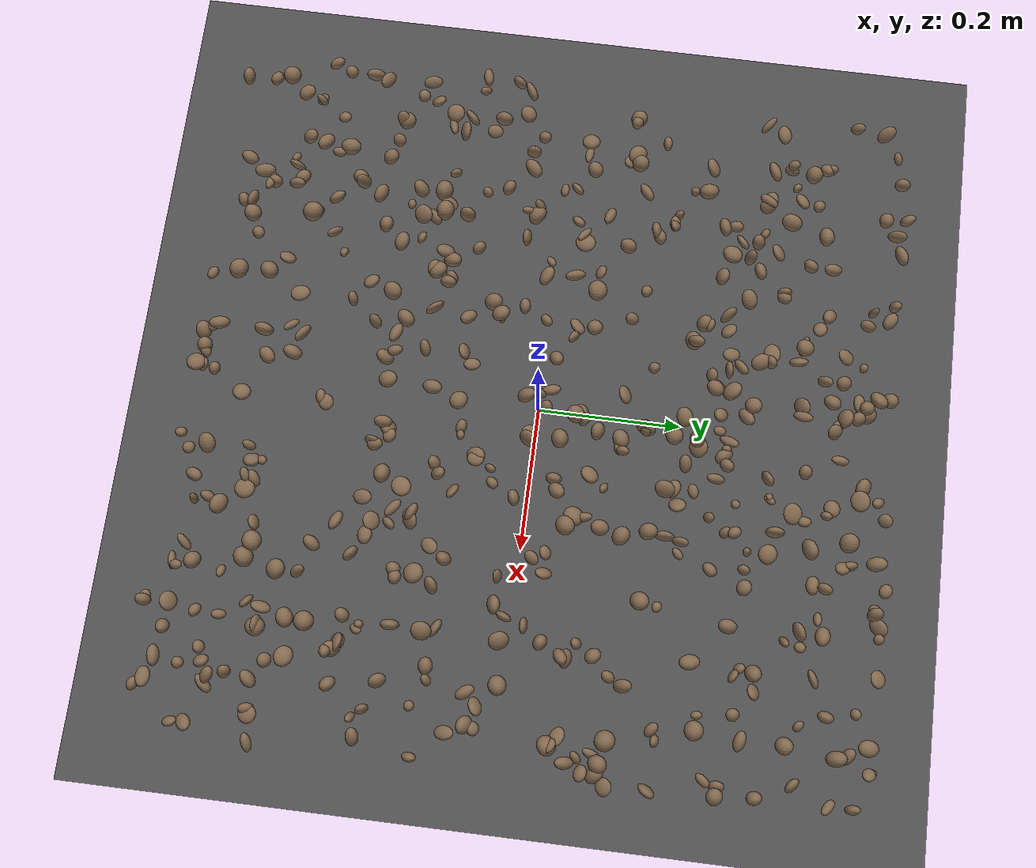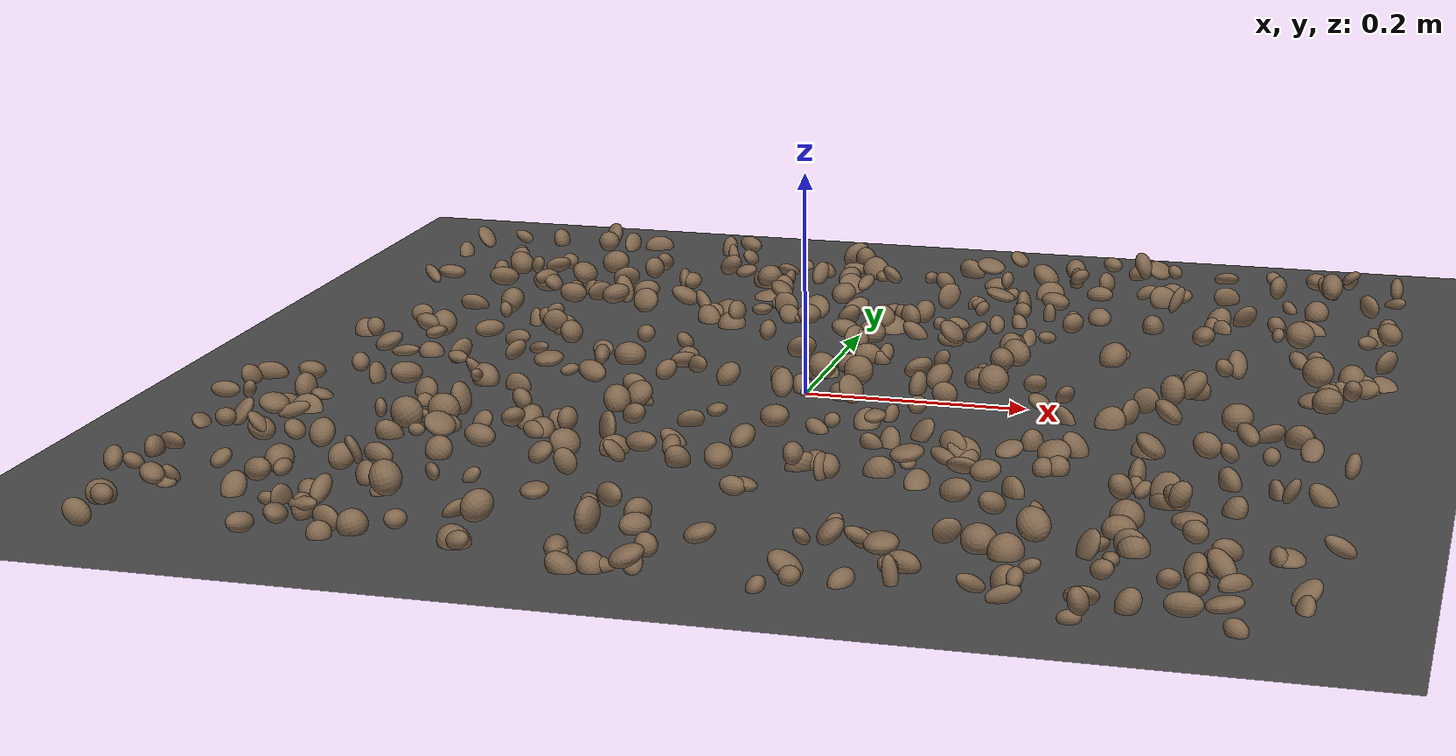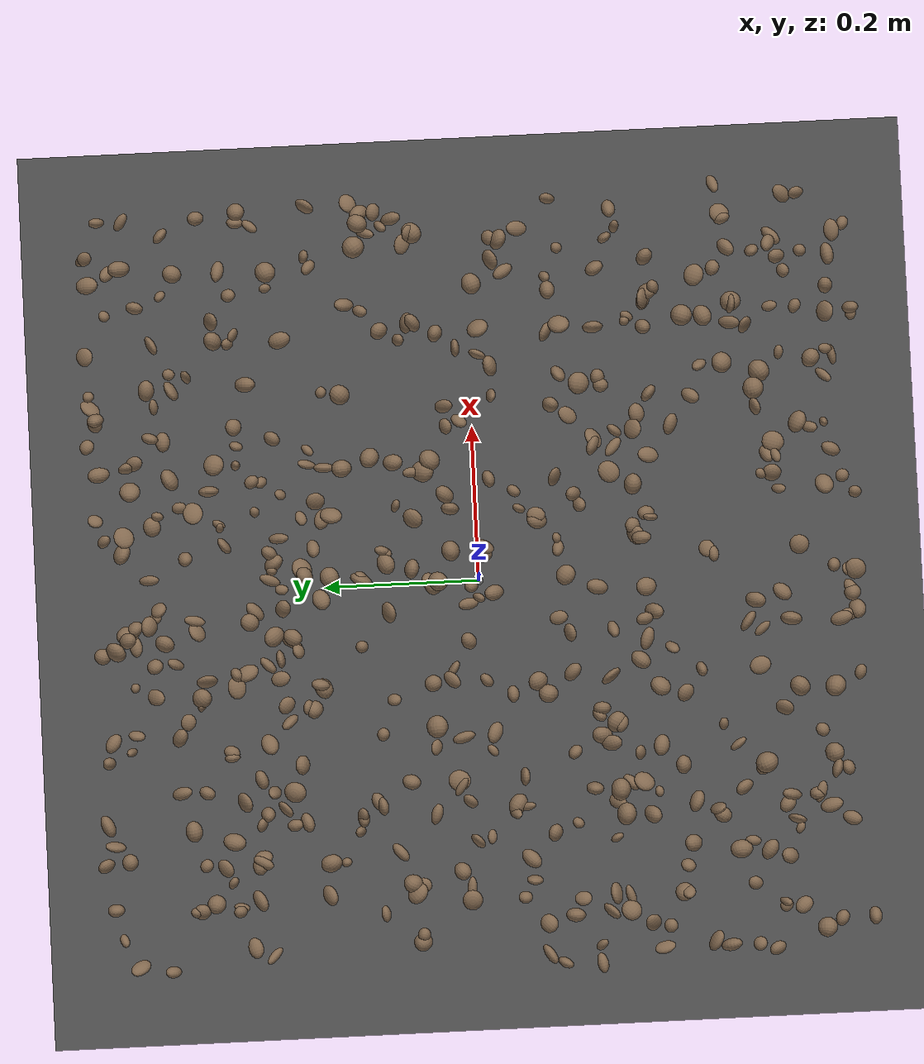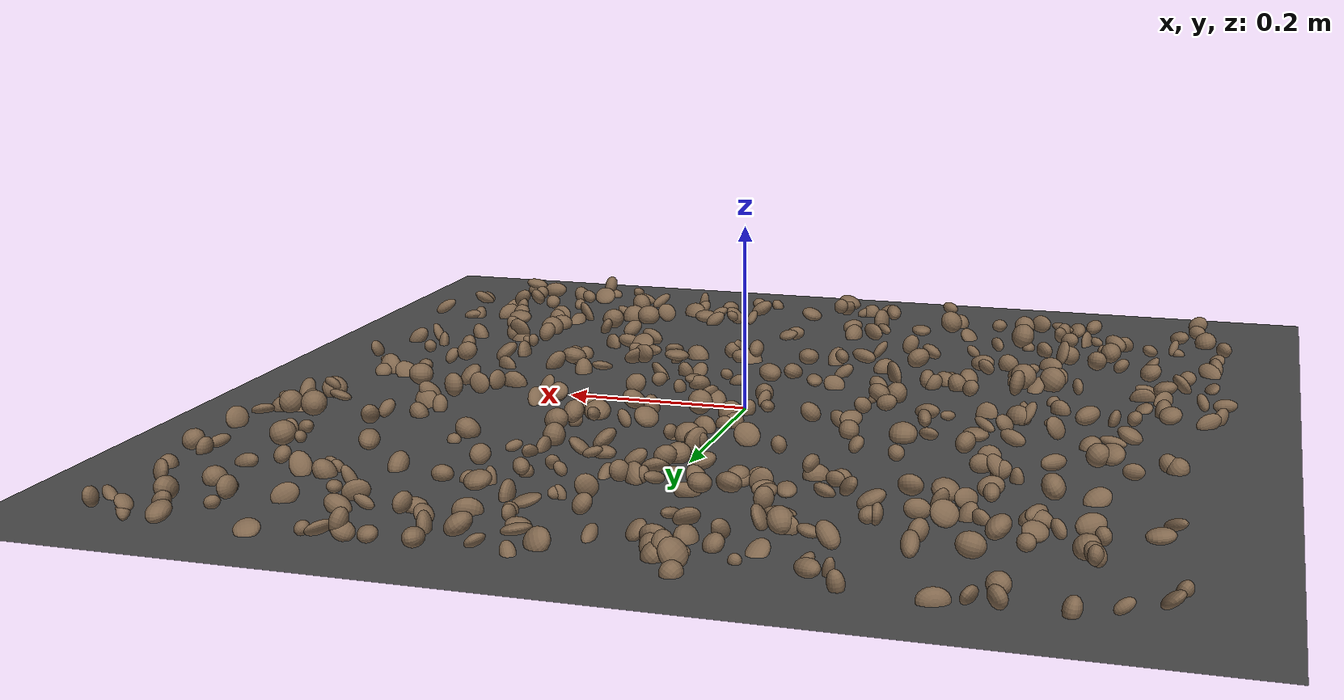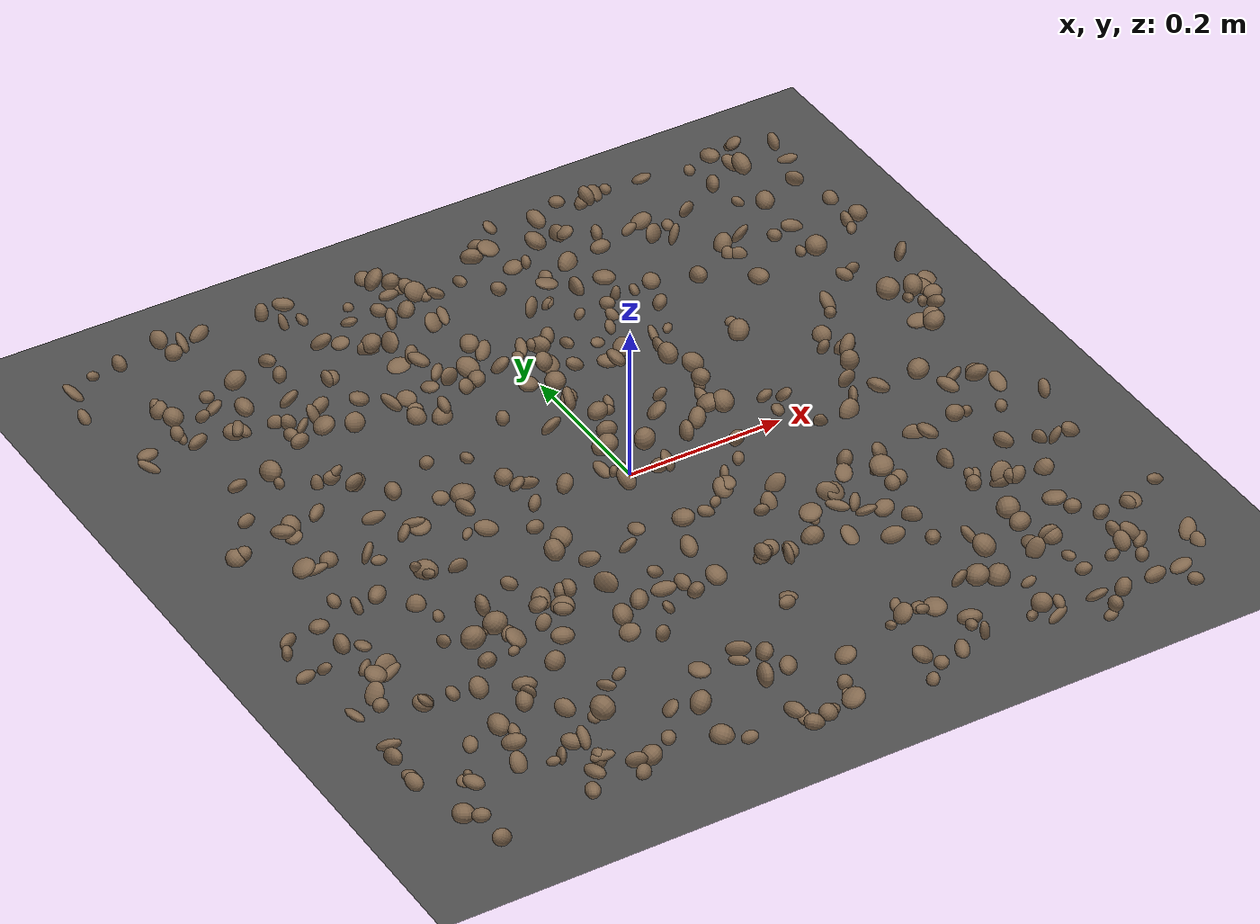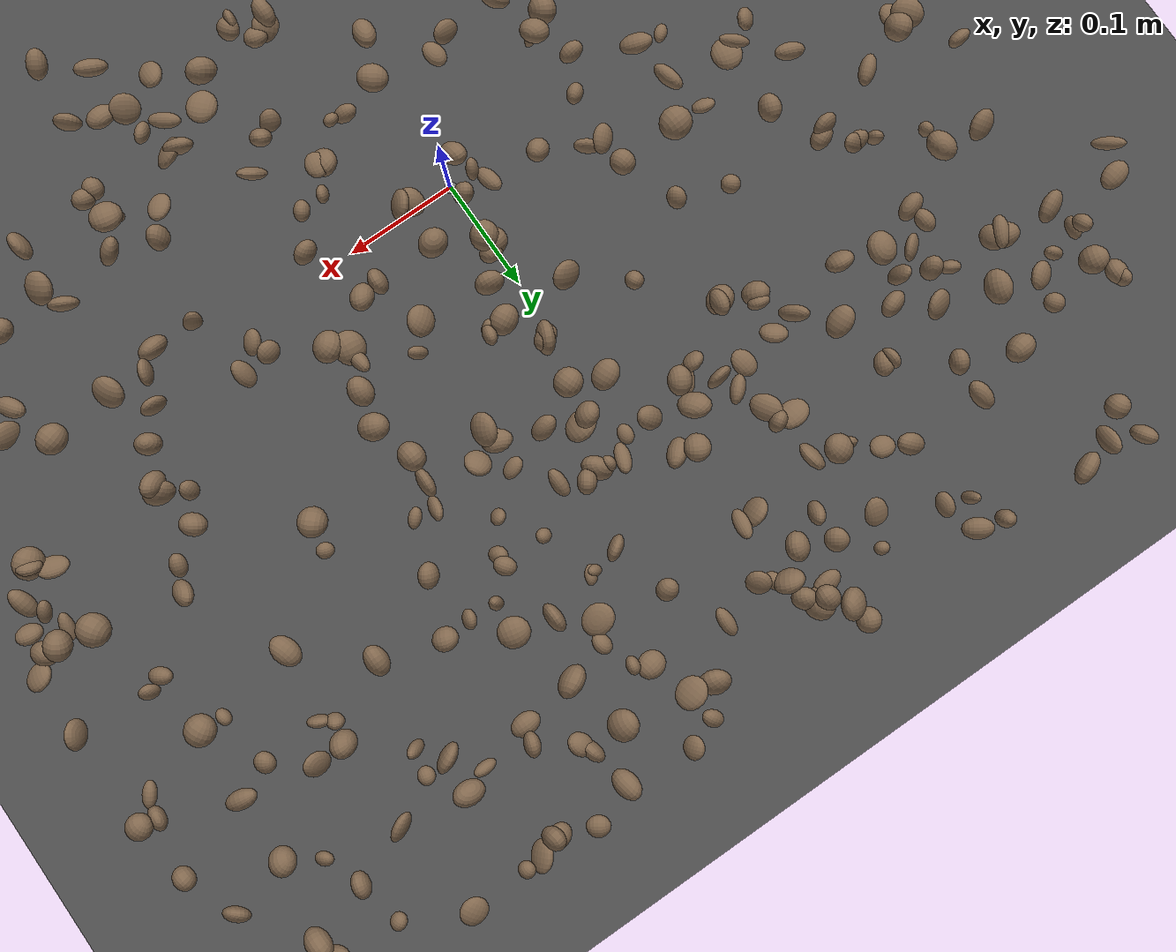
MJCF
<mujoco model="rocky_terrain_scene">
    <compiler angle="radian" inertiafromgeom="true" />
    <option timestep="0.002" gravity="0 0 -9.81" />

    <worldbody>
        <light name="sunlight" pos="5 5 5" dir="-1 -1 -1" diffuse="1 1 1" specular="0.5 0.5 0.5" ambient="0.5 0.5 0.5" />

        <geom name="ground_plane" type="plane" size="50 50 0.1" rgba="0.3 0.3 0.3 1" />

        <body name="rocky_terrain_body">

        <geom name="rock1" type="ellipsoid" size="0.014472520199706105 0.009326303582320727 0.009813545633023729" pos="0.16031238314202645 0.4847533013972535 0.006094840191771471" quat="0.17687824306913588 0.279265042733348 0.2723538680336561 0.2715028461638599" rgba="0.5 0.4 0.3 1" /><geom name="rock2" type="ellipsoid" size="0.013728827206437706 0.00509452618307271 0.009002680826756686" pos="-0.48259018358034345 -0.216499340233282 0.001039292472366979" quat="0.1470945351667251 0.2922739576437685 0.36596198874364766 0.1946695184458587" rgba="0.5 0.4 0.3 1" /><geom name="rock3" type="ellipsoid" size="0.011430843128636087 0.009091204816389517 0.012047047167694225" pos="0.017430171197993394 0.2247038519896214 0.013610749291578524" quat="0.0993262459593458 0.5316378101358564 0.2050171108166444 0.16401883308815343" rgba="0.5 0.4 0.3 1" /><geom name="rock4" type="ellipsoid" size="0.009959368689476672 0.009726375118919236 0.009013071977744605" pos="0.24619345991953412 -0.16917587080402186 0.002520854243415412" quat="0.2803945850146773 0.2534718213986026 0.20757797221292384 0.25855562137379623" rgba="0.5 0.4 0.3 1" /><geom name="rock5" type="ellipsoid" size="0.006521550975099131 0.012275815740656159 0.013875670382172776" pos="0.26486929688660965 0.3866510904293531 0.006498739177210732" quat="0.19544352599794101 0.18512828102089293 0.3951350376128087 0.22429315536835742" rgba="0.5 0.4 0.3 1" /><geom name="rock6" type="ellipsoid" size="0.0111332699780414 0.0059043854528781315 0.01029706700018022" pos="-0.3885867850238016 0.0905201875278615 0.006158591956107235" quat="0.28923848866894564 0.17598256023438252 0.24697942774516093 0.28779952335151093" rgba="0.5 0.4 0.3 1" /><geom name="rock7" type="ellipsoid" size="0.011844572256966477 0.006093460384653252 0.014227389208623487" pos="0.41606789866705973 -0.033883886951700526 0.0030106338277999965" quat="0.4658078256640949 0.07753575490674976 0.25271109603484776 0.2039453233943076" rgba="0.5 0.4 0.3 1" /><geom name="rock8" type="ellipsoid" size="0.00875392375438113 0.01245410320702367 0.005278700385687181" pos="-0.41247429927561285 -0.2496435653169905 0.014900439232179485" quat="0.3071432248362091 0.15388608902402534 0.1586041683101522 0.3803665178296134" rgba="0.5 0.4 0.3 1" /><geom name="rock9" type="ellipsoid" size="0.011585943410784613 0.009604187000410167 0.012168826942548956" pos="-0.24944326381559312 -0.25205051449917104 0.00498742508246053" quat="0.05363777002887682 0.2230660524462636 0.08209428222332617 0.6412018953015334" rgba="0.5 0.4 0.3 1" /><geom name="rock10" type="ellipsoid" size="0.010624552731051633 0.006255390175140137 0.00570686664478324" pos="-0.475411309373977 -0.1357239905582467 0.007433566332784767" quat="0.3026190411370336 0.039086757118827226 0.42177340042720607 0.23652080131693307" rgba="0.5 0.4 0.3 1" /><geom name="rock11" type="ellipsoid" size="0.012225228033389433 0.012731184771192236 0.011052230907364973" pos="0.2684013249368252 -0.44258345426519563 0.004500712490441478" quat="0.04366766104889681 0.22935591245337733 0.35323054275915977 0.373745883738566" rgba="0.5 0.4 0.3 1" /><geom name="rock12" type="ellipsoid" size="0.0072823980581593496 0.01107396795178512 0.00940141858603031" pos="-0.29965258652604043 0.16275581332196842 0.007884021070669517" quat="0.3903379303689765 0.15458796082027892 0.05568225079131723 0.3993918580194274" rgba="0.5 0.4 0.3 1" /><geom name="rock13" type="ellipsoid" size="0.006196544880692253 0.013812111110405378 0.005372085934543863" pos="0.28124226272460917 0.36643167996979176 0.01164827666345132" quat="0.32051895095565586 0.33417169543326375 0.25508318895472415 0.09022616465635629" rgba="0.5 0.4 0.3 1" /><geom name="rock14" type="ellipsoid" size="0.0061138370925657 0.010669736044217797 0.012727629399666809" pos="-0.3544854541072554 0.3426404044748492 0.013118776109131992" quat="0.0432910781207666 0.30202836323359483 0.2292391367123666 0.42544142193327195" rgba="0.5 0.4 0.3 1" /><geom name="rock15" type="ellipsoid" size="0.008507586041693778 0.012593386740087498 0.012287904895613419" pos="0.39841057457629336 -0.16822726997049742 0.00380140156829382" quat="0.34223735336951 0.4354191368795176 0.05676774587503526 0.16557576387593723" rgba="0.5 0.4 0.3 1" /><geom name="rock16" type="ellipsoid" size="0.009210160656920627 0.007545682302889693 0.00838282106638719" pos="-0.21299350882207346 -0.4330657372463569 0.007583759531584165" quat="0.29887460139751015 0.4145681117584543 0.1500333237611254 0.1365239630829101" rgba="0.5 0.4 0.3 1" /><geom name="rock17" type="ellipsoid" size="0.01332026837409819 0.012758360105664609 0.014384767709051238" pos="-0.15695918503533068 -0.4532773140721347 0.0008178167181482343" quat="0.2740623072823865 0.2543636379753064 0.4229889283066444 0.04858512643566262" rgba="0.5 0.4 0.3 1" /><geom name="rock18" type="ellipsoid" size="0.009674882130088762 0.005622268295319355 0.01099249872137791" pos="-0.16458330702730517 0.3827276326822098 0.009011427355430231" quat="0.2776636411089833 0.2641507935701532 0.17805228930786776 0.28013327601299576" rgba="0.5 0.4 0.3 1" /><geom name="rock19" type="ellipsoid" size="0.009189865439541638 0.006823748753727156 0.0057088422288149665" pos="-0.029739023545353405 0.421113616072605 0.00246202880259447" quat="0.40055578700497046 0.0013947688716348364 0.03835837925353364 0.559691064869861" rgba="0.5 0.4 0.3 1" /><geom name="rock20" type="ellipsoid" size="0.012890051340808773 0.01406444148325674 0.011631147348197021" pos="-0.15587640325315266 -0.4064438506369229 0.014639960877055744" quat="0.30537342809117385 0.31426923960417563 0.34822353586528243 0.032133796439368124" rgba="0.5 0.4 0.3 1" /><geom name="rock21" type="ellipsoid" size="0.013338276241247532 0.011840242840676037 0.008526617962327378" pos="0.3644099327039586 -0.23535525429167836 0.00964073537638554" quat="0.41063243415550743 0.0058716769178681055 0.24421277574184821 0.33928311318477616" rgba="0.5 0.4 0.3 1" /><geom name="rock22" type="ellipsoid" size="0.011695265751488574 0.01143105133398034 0.012535113697013161" pos="-0.46106322693179147 0.09412394735897389 0.0012325416431200247" quat="0.20806681988948342 0.4527899586372013 0.2878132977234714 0.05132992374984377" rgba="0.5 0.4 0.3 1" /><geom name="rock23" type="ellipsoid" size="0.012085293326150806 0.012263578928947892 0.009627976056202336" pos="-0.4127705478633692 -0.24474619027946376 0.00887131541963043" quat="0.5007817761665722 0.014271966670014279 0.1441536161238386 0.3407926410395751" rgba="0.5 0.4 0.3 1" /><geom name="rock24" type="ellipsoid" size="0.014166442540241814 0.010938881343692877 0.012383872051774391" pos="-0.35450420328671106 0.20685219141120947 0.010476447558496622" quat="0.35655613073627973 0.017449910138079356 0.16678878039441078 0.4592051787312301" rgba="0.5 0.4 0.3 1" /><geom name="rock25" type="ellipsoid" size="0.005603407521116428 0.014690566565427336 0.010222976314203335" pos="-0.13011806028252737 0.42402980654441746 0.0005809413419150766" quat="0.17660783948864317 0.3622721144064956 0.07162816866250189 0.38949187744235936" rgba="0.5 0.4 0.3 1" /><geom name="rock26" type="ellipsoid" size="0.010647900881413486 0.011974217848378474 0.007287363555589156" pos="-0.3442927226010031 0.4960160053380287 0.010835911461068534" quat="0.24965947282809706 0.04298883699927509 0.4820076338214778 0.22534405635115004" rgba="0.5 0.4 0.3 1" /><geom name="rock27" type="ellipsoid" size="0.014473499351856094 0.009797795524622361 0.009190194708398595" pos="-0.014953030328355488 -0.15199178201293684 0.004572140122382404" quat="0.004567775640865694 0.4867878444688182 0.3745613250036604 0.13408305488665567" rgba="0.5 0.4 0.3 1" /><geom name="rock28" type="ellipsoid" size="0.005875259624616932 0.014275944545153369 0.008918962793523933" pos="0.31978083295382964 -0.33958548443173786 0.0013304821917709884" quat="0.08150127269989757 0.30141201526440886 0.07993849200656247 0.5371482200291311" rgba="0.5 0.4 0.3 1" /><geom name="rock29" type="ellipsoid" size="0.010562800773791577 0.005680594838141948 0.012113852225408075" pos="-0.07227751360587953 -0.1142707805824219 0.0035547722216824973" quat="0.45322823031896065 0.07451347718648532 0.3151184512921208 0.15713984120243327" rgba="0.5 0.4 0.3 1" /><geom name="rock30" type="ellipsoid" size="0.011278625007623456 0.00508049963180952 0.013892963819738976" pos="0.24629301831025607 0.4917688888780566 0.008807615683127074" quat="0.0020968349527615083 0.2825033003052316 0.32652206595949773 0.38887779878250917" rgba="0.5 0.4 0.3 1" /><geom name="rock31" type="ellipsoid" size="0.005834256905391718 0.013004558871208521 0.010812522432696259" pos="0.06055280050333767 0.3264576559213036 0.011336739419328236" quat="0.1403013328213773 0.21436654137269762 0.43467339755729156 0.21065872824863338" rgba="0.5 0.4 0.3 1" /><geom name="rock32" type="ellipsoid" size="0.007763106292929404 0.013985743098442832 0.008415771596099403" pos="0.42084679477717035 0.46243970770849074 0.007767910153179137" quat="0.33851146411939087 0.00017234286369487633 0.35207505424196245 0.3092411387749518" rgba="0.5 0.4 0.3 1" /><geom name="rock33" type="ellipsoid" size="0.014737030592091777 0.009628664068122078 0.0075725322677133566" pos="0.3657673831203996 0.15785117061448128 0.009147815022648931" quat="0.2818048999395287 0.2717247484067396 0.0018895192419547556 0.4445808324117768" rgba="0.5 0.4 0.3 1" /><geom name="rock34" type="ellipsoid" size="0.008671621995501363 0.00510727534097554 0.005421899318063979" pos="-0.21944207363415325 -0.007651050692812356 0.008308806771055492" quat="0.4030645614933582 0.3346974005991424 0.08817242293950993 0.1740656149679896" rgba="0.5 0.4 0.3 1" /><geom name="rock35" type="ellipsoid" size="0.0132947798836636 0.011747444930865492 0.006059321790211972" pos="0.1564200509142296 0.19385764441289255 0.0012159478380455151" quat="0.2811459460994105 0.230062556082393 0.22592675424460085 0.26286474357359557" rgba="0.5 0.4 0.3 1" /><geom name="rock36" type="ellipsoid" size="0.0056713062926124725 0.0061639281479241685 0.009160143152783084" pos="-0.19956066965564612 -0.30624278502951974 0.0033501147277360285" quat="0.49263389371153377 0.10060355342893376 0.20844766719946167 0.19831488566007074" rgba="0.5 0.4 0.3 1" /><geom name="rock37" type="ellipsoid" size="0.011753900877581037 0.009619827283844546 0.00662399129412817" pos="0.17232368121764396 0.43807247602726307 0.010381933839896584" quat="0.18682349905288242 0.2633533227597384 0.5275980425206522 0.022225135666726827" rgba="0.5 0.4 0.3 1" /><geom name="rock38" type="ellipsoid" size="0.014627775111725742 0.008991234839305522 0.010608130925958071" pos="0.3235238653930631 0.24345569919909238 0.010285978042103268" quat="0.27999791552180564 0.1429976781502151 0.2684384729916693 0.30856593333631" rgba="0.5 0.4 0.3 1" /><geom name="rock39" type="ellipsoid" size="0.005728121513601346 0.010778809589238346 0.013666334448933701" pos="-0.43298671409890943 -0.1504397221774375 0.0006696465708478899" quat="0.05579729291691355 0.22536562686304717 0.43084201718909926 0.2879950630309401" rgba="0.5 0.4 0.3 1" /><geom name="rock40" type="ellipsoid" size="0.007425457461665487 0.006928941514471964 0.010009926049329137" pos="-0.14126923037706485 -0.48524580637016546 0.014540035184130306" quat="0.2537746356882083 0.3042149524615867 0.09805146752956687 0.3439589443206381" rgba="0.5 0.4 0.3 1" /><geom name="rock41" type="ellipsoid" size="0.01073014438528929 0.008942649453146358 0.013741774583555424" pos="0.4103052827907272 -0.23398734261298593 0.0013351320297532814" quat="0.28527026818327034 0.1780604749131667 0.004985440693309373 0.5316838162102536" rgba="0.5 0.4 0.3 1" /><geom name="rock42" type="ellipsoid" size="0.011527821784322424 0.0067229195047847565 0.007254039448022708" pos="0.0740854972041981 0.4823352397729116 2.877940914860988e-05" quat="0.29657998603424846 0.07636092866359158 0.429496894740982 0.1975621905611779" rgba="0.5 0.4 0.3 1" /><geom name="rock43" type="ellipsoid" size="0.01378217495262337 0.012641655291096846 0.011238277514713582" pos="0.15368353515059274 0.17063236105232982 0.007423467689138067" quat="0.1075911982416665 0.3579867315198588 0.11251808480858172 0.42190398542989294" rgba="0.5 0.4 0.3 1" /><geom name="rock44" type="ellipsoid" size="0.011720116272186188 0.013482472540451717 0.01294660528616405" pos="0.47069301197357527 0.13584538681499814 0.00865538135079247" quat="0.13654511106814937 0.11812897160609725 0.5033930264696143 0.24193289085613912" rgba="0.5 0.4 0.3 1" /><geom name="rock45" type="ellipsoid" size="0.013056185114329506 0.013497733440892976 0.012692660532194193" pos="0.34710773817042107 -0.34278824604173463 0.0016109955557456128" quat="0.05142745132047521 0.3254752360475428 0.1494313321650627 0.47366598046691927" rgba="0.5 0.4 0.3 1" /><geom name="rock46" type="ellipsoid" size="0.011189468536646183 0.007303470538393591 0.008711008826755554" pos="-0.059483572850836164 -0.2110232177194291 0.011323663140669819" quat="0.317037436027513 0.16793657290454436 0.0838043219460527 0.4312216691218899" rgba="0.5 0.4 0.3 1" /><geom name="rock47" type="ellipsoid" size="0.00979072740950083 0.005092253812263451 0.010014606818600573" pos="0.10026114416672727 0.49137230997657355 0.01164452095437181" quat="0.02695246753576289 0.28765749383550704 0.34123409114526637 0.3441559474834636" rgba="0.5 0.4 0.3 1" /><geom name="rock48" type="ellipsoid" size="0.014713197615997368 0.00937479390145814 0.012334414438866272" pos="-0.059506962788746565 0.26744903411902676 0.00692810299237537" quat="0.14940955271787917 0.2034001513940724 0.1961570236130898 0.45103327227495865" rgba="0.5 0.4 0.3 1" /><geom name="rock49" type="ellipsoid" size="0.008105555301102327 0.007487775941450796 0.012694157864021224" pos="-0.212656053579666 0.4870980395931279 0.004961186513528137" quat="0.24907754502131635 0.0006041511344912168 0.08658897134586026 0.6637293324983322" rgba="0.5 0.4 0.3 1" /><geom name="rock50" type="ellipsoid" size="0.006932780260013811 0.006614616064400546 0.01408657207577214" pos="0.4998503209754045 -0.32659791227694523 0.01162162745420396" quat="0.19523452860616086 0.19498531386068368 0.4330515844085174 0.17672857312463808" rgba="0.5 0.4 0.3 1" /><geom name="rock51" type="ellipsoid" size="0.006520536157325243 0.010215330991350201 0.007337283863407009" pos="0.04177821416692995 0.11834436260038184 0.0008626956520537398" quat="0.21834670165739134 0.20177246769977839 0.18667683061287682 0.39320400002995337" rgba="0.5 0.4 0.3 1" /><geom name="rock52" type="ellipsoid" size="0.0074309722870883384 0.012944929679342528 0.0050448092629294585" pos="0.1616520852534592 0.21587843749070956 0.002723615342413928" quat="0.5204266630062059 0.16613421942630593 0.2661385250919556 0.04730059247553263" rgba="0.5 0.4 0.3 1" /><geom name="rock53" type="ellipsoid" size="0.009795037085601121 0.013675907322731884 0.009962703878360013" pos="0.11319674739004026 0.039210516533965234 0.013264551006558996" quat="0.3230367532393976 0.25206514173643835 0.39488585411504706 0.030012250909116956" rgba="0.5 0.4 0.3 1" /><geom name="rock54" type="ellipsoid" size="0.01372686367424842 0.009161649273988229 0.014659105814143703" pos="-0.07006258737966808 0.47205118622593467 0.010562172504520155" quat="0.4698582190431259 0.07914378002211969 0.17754902657122168 0.2734489743635327" rgba="0.5 0.4 0.3 1" /><geom name="rock55" type="ellipsoid" size="0.00866841232570636 0.014782162674150539 0.009048507216402995" pos="0.4754196981682114 -0.19058216098658243 0.0032037757319102527" quat="0.29161978368014685 0.04585555329893959 0.2497888687693329 0.4127357942515806" rgba="0.5 0.4 0.3 1" /><geom name="rock56" type="ellipsoid" size="0.0074463183195381515 0.009858892747626965 0.014288089472957004" pos="0.19083968926658545 -0.25652765014457457 0.008160416089646138" quat="0.39725134302856424 0.20587298048323363 0.2519320415506352 0.14494363493756693" rgba="0.5 0.4 0.3 1" /><geom name="rock57" type="ellipsoid" size="0.00929576257196129 0.012998479039165792 0.005858516037172975" pos="0.4380129438535759 -0.18332283610417854 0.001103767383489048" quat="0.18680402160655216 0.16694807745174214 0.295418503381101 0.35082939756060477" rgba="0.5 0.4 0.3 1" /><geom name="rock58" type="ellipsoid" size="0.0060990235913812 0.01294716481034449 0.012900810824389073" pos="-0.04901338310278813 0.3667157806169973 0.004983513671297098" quat="0.27534156239417645 0.10650664922789979 0.4154273251649347 0.20272446321298918" rgba="0.5 0.4 0.3 1" /><geom name="rock59" type="ellipsoid" size="0.006297333634972167 0.007830330423087044 0.005688400140837563" pos="0.10230230163093379 0.2853827786045531 0.011620246334421951" quat="0.21166193587364165 0.34230411151606016 0.32311711667101384 0.12291683593928437" rgba="0.5 0.4 0.3 1" /><geom name="rock60" type="ellipsoid" size="0.01337766794246498 0.010429296935837332 0.010699646518036638" pos="0.157675525545093 0.10408159029280428 0.014126027994711077" quat="0.256350166418391 0.30043160640677835 0.3744295165509799 0.0687887106238509" rgba="0.5 0.4 0.3 1" /><geom name="rock61" type="ellipsoid" size="0.009463705371874798 0.006569088016893576 0.008994670359559254" pos="-0.4837393936186748 -0.33892133719359385 0.00313409010108364" quat="0.37826114484797196 0.28952943833401396 0.2719035012059263 0.06030591561208771" rgba="0.5 0.4 0.3 1" /><geom name="rock62" type="ellipsoid" size="0.005766372258290699 0.006321257663992079 0.00679654275210105" pos="-0.11711869378178552 0.4494099095082893 0.0005523615124384473" quat="0.14210297861213222 0.47716904376375996 0.3213915958581407 0.059336381765967096" rgba="0.5 0.4 0.3 1" /><geom name="rock63" type="ellipsoid" size="0.006804404017238627 0.013146925452314027 0.011777659073897336" pos="0.16774425830722706 0.447538760281759 0.004055781906071969" quat="0.35087057076662315 0.5364604566281207 0.08572815190561636 0.026940820699639715" rgba="0.5 0.4 0.3 1" /><geom name="rock64" type="ellipsoid" size="0.008952731129369323 0.012724327159983218 0.012681849189417276" pos="-0.43570802209108817 -0.10370191940653395 0.0035510727882190757" quat="0.04255502363156705 0.002439526318535344 0.37326235075497644 0.5817430992949213" rgba="0.5 0.4 0.3 1" /><geom name="rock65" type="ellipsoid" size="0.009177488648587523 0.013361758049733701 0.013761058270704056" pos="0.0567006950190474 0.4594672019771693 0.003923461204897485" quat="0.14032852784898023 0.43040430411989844 0.19934510617974688 0.22992206185137445" rgba="0.5 0.4 0.3 1" /><geom name="rock66" type="ellipsoid" size="0.0079513910743668 0.00872465037606698 0.011346310207871312" pos="0.3681464531700651 -0.24216018100198844 0.014741944640516693" quat="0.40766886435713323 0.09958205900039387 0.12463647390989414 0.36811260273257873" rgba="0.5 0.4 0.3 1" /><geom name="rock67" type="ellipsoid" size="0.0055947685584583655 0.005523331934810221 0.009342726621631534" pos="0.17957474226115688 0.21375673361765257 0.006874368135381123" quat="0.17016862697957452 0.11600854662528093 0.4156773801526211 0.2981454462425233" rgba="0.5 0.4 0.3 1" /><geom name="rock68" type="ellipsoid" size="0.01469441716243564 0.009913065795277058 0.006323521220306081" pos="-0.068831596544503 -0.34415582678237344 0.010799436910180382" quat="0.1541440965723818 0.08899401379342595 0.39401260264646826 0.362849286987724" rgba="0.5 0.4 0.3 1" /><geom name="rock69" type="ellipsoid" size="0.012895945535775711 0.013713940180125082 0.00771943378994987" pos="-0.4103069176237236 0.027956273722312908 0.012402145439590105" quat="0.08441290222029128 0.4056146681268405 0.4113686959499933 0.0986037337028749" rgba="0.5 0.4 0.3 1" /><geom name="rock70" type="ellipsoid" size="0.00802692681121939 0.010266647085630128 0.011111704875431689" pos="0.1963465715278635 0.2588702818990264 0.010175129461764736" quat="0.011460160363242074 0.23879577478288197 0.42305945844952264 0.3266846064043533" rgba="0.5 0.4 0.3 1" /><geom name="rock71" type="ellipsoid" size="0.013922813276498067 0.01177455846400499 0.014577453439964635" pos="-0.1853638845324369 0.06287327944165999 0.00566926698804162" quat="0.28704160122210426 0.19752935454703416 0.3014835711162606 0.21394547311460088" rgba="0.5 0.4 0.3 1" /><geom name="rock72" type="ellipsoid" size="0.007170629320099518 0.010346284064147747 0.006872213046306693" pos="0.14117926550555815 0.27607778271466665 0.0012180730026484488" quat="0.4671388188033736 0.21353506715030063 0.11882629073499143 0.20049982331133442" rgba="0.5 0.4 0.3 1" /><geom name="rock73" type="ellipsoid" size="0.014562886839610774 0.014725455869157862 0.013209445611999944" pos="0.25512205381502173 -0.37465879903158217 0.0026316868342536664" quat="0.33311394232627606 0.42984948642960846 0.03693770079834933 0.20009887044576602" rgba="0.5 0.4 0.3 1" /><geom name="rock74" type="ellipsoid" size="0.013495616331753744 0.005786009911076176 0.013132342059939087" pos="0.3277288022427768 -0.4640466498949988 0.006383863891439612" quat="0.17319119647719822 0.04646460894013691 0.5413409647689713 0.23900322981369346" rgba="0.5 0.4 0.3 1" /><geom name="rock75" type="ellipsoid" size="0.006887301129408309 0.014249504005826186 0.005543256681351979" pos="-0.2928925511277235 -0.42678962103370743 0.011240706801288677" quat="0.015253404760542745 0.5297163598453954 0.38899581901046987 0.06603441638359189" rgba="0.5 0.4 0.3 1" /><geom name="rock76" type="ellipsoid" size="0.008722816775045841 0.009721184021108413 0.010195829197692935" pos="0.39061178172589317 -0.3209423669426037 0.012219016041022294" quat="0.20673019394029918 0.3944197354146764 0.1099709936811516 0.2888790769638728" rgba="0.5 0.4 0.3 1" /><geom name="rock77" type="ellipsoid" size="0.008306194831651213 0.010322527246815651 0.012302949809820742" pos="-0.4547499191360249 -0.4880051677826561 0.010661192564574642" quat="0.15238195206300656 0.32733157012680064 0.36110615786931205 0.15918031994088072" rgba="0.5 0.4 0.3 1" /><geom name="rock78" type="ellipsoid" size="0.009608395605937563 0.006244475839682886 0.01284172792953539" pos="-0.12612401805517215 0.04071866034677907 0.011044405499202551" quat="0.2705830781049889 0.00641100417737914 0.445152651111008 0.2778532666066239" rgba="0.5 0.4 0.3 1" /><geom name="rock79" type="ellipsoid" size="0.010550712352258445 0.006359340154705053 0.012064604966275542" pos="-0.14851236530539735 0.255261549944668 0.0029451995243038225" quat="0.27966390220879134 0.3997509549957596 0.043318561187718416 0.27726658160773066" rgba="0.5 0.4 0.3 1" /><geom name="rock80" type="ellipsoid" size="0.014189270849885516 0.007878489881647846 0.013303851700254839" pos="-0.00804854137452271 -0.4855928453877728 0.014086563560322762" quat="0.4117466469400915 0.39103900977290995 0.016765478090999535 0.180448865195999" rgba="0.5 0.4 0.3 1" /><geom name="rock81" type="ellipsoid" size="0.010606188770404106 0.008387108138294566 0.008182034456765568" pos="-0.45570326143679885 -0.445605003772114 0.011451005575657624" quat="0.13427904908740546 0.06068802577274218 0.3150230095229551 0.4900099156168973" rgba="0.5 0.4 0.3 1" /><geom name="rock82" type="ellipsoid" size="0.009168905132964431 0.007005566839372611 0.008793488892507738" pos="0.3833855169052641 -0.4123906947135745 0.0063595748674231565" quat="0.5053292072452855 0.17235757945824107 0.19934758488635115 0.12296562841012224" rgba="0.5 0.4 0.3 1" /><geom name="rock83" type="ellipsoid" size="0.01371250829661885 0.012784062211628505 0.010425251920588227" pos="-0.14710732637626134 -0.22718633756424278 0.01162084181034506" quat="0.46958181259755954 0.20255417004419662 0.11380129179086104 0.21406272556738276" rgba="0.5 0.4 0.3 1" /><geom name="rock84" type="ellipsoid" size="0.008528037570829275 0.014568639614181686 0.005684622964325654" pos="-0.26023885496186994 0.27555783183309146 0.010237658283933117" quat="0.43656475447635196 0.2878539269057578 0.09781400934568935 0.1777673092722009" rgba="0.5 0.4 0.3 1" /><geom name="rock85" type="ellipsoid" size="0.010659305807338332 0.014008230492075287 0.00831509819002492" pos="0.2306330849342778 0.4853510321442288 0.014124646639447326" quat="0.30797845270083424 0.18024066076241488 0.2343316700077289 0.27744921652902205" rgba="0.5 0.4 0.3 1" /><geom name="rock86" type="ellipsoid" size="0.008611938830739877 0.011711572697240356 0.0062588473997124364" pos="0.4918808719517157 -0.1116740514337371 0.0063771753576576" quat="0.2959192452120945 0.1850830180771256 0.368010032916717 0.15098770379406276" rgba="0.5 0.4 0.3 1" /><geom name="rock87" type="ellipsoid" size="0.014062564585744963 0.011743920769439042 0.01248003322299042" pos="0.24958647940780443 0.16886773694406187 0.005550545670581954" quat="0.296532906473652 0.39117275653302247 0.027379918883998162 0.2849144181093273" rgba="0.5 0.4 0.3 1" /><geom name="rock88" type="ellipsoid" size="0.014883938400876574 0.01242101944632929 0.00585157601542592" pos="0.17706513470056529 -0.1560647022307725 0.009168838169141578" quat="0.5936000526626644 0.22290385781713182 0.1550026394740383 0.02849345004616554" rgba="0.5 0.4 0.3 1" /><geom name="rock89" type="ellipsoid" size="0.006658704640758639 0.008752044448826345 0.00504574289138165" pos="0.0006111389296927783 0.25504950441328 0.007914994711023431" quat="0.060181798525713745 0.06820731667212523 0.05291313962035719 0.8186977451818038" rgba="0.5 0.4 0.3 1" /><geom name="rock90" type="ellipsoid" size="0.01265049476894458 0.007570791724392544 0.009912662746290326" pos="-0.4366593534584813 -0.3970041081825123 0.014950887543709046" quat="0.10340492245902774 0.20256543348169506 0.35726642664231556 0.3367632174169617" rgba="0.5 0.4 0.3 1" /><geom name="rock91" type="ellipsoid" size="0.012751801298266412 0.010386146940452957 0.00749444819881181" pos="-0.2820683792344313 -0.32875947889759416 0.005359097736113401" quat="0.06803242164769217 0.26575810626080043 0.3632642532976528 0.30294521879385455" rgba="0.5 0.4 0.3 1" /><geom name="rock92" type="ellipsoid" size="0.013022943790315909 0.013527037182951465 0.00599800017679517" pos="0.0438439293981685 -0.008888290768797602 0.009918452274781709" quat="0.479346479581506 0.20362313370726084 0.2061322070768581 0.11089817963437501" rgba="0.5 0.4 0.3 1" /><geom name="rock93" type="ellipsoid" size="0.00826455788237937 0.008151415731276685 0.011333158583762033" pos="-0.1928690727846708 -0.1748240918009336 0.0030301159797726882" quat="0.3054243111618607 0.2957494385681668 0.2544375523682606 0.14438869790171188" rgba="0.5 0.4 0.3 1" /><geom name="rock94" type="ellipsoid" size="0.006350218203701512 0.012140267244663603 0.013396357142529312" pos="0.31923661709376006 -0.10131361339921374 9.346892033348764e-05" quat="0.303889939152918 0.32250848780983343 0.23401465844895084 0.1395869145882977" rgba="0.5 0.4 0.3 1" /><geom name="rock95" type="ellipsoid" size="0.00921243433906762 0.011249539987196487 0.005984030341530528" pos="-0.28349677799271933 0.024486849266546207 0.013669010382833089" quat="0.2916137409040399 0.28899359189163615 0.3926842508786716 0.026708416325652285" rgba="0.5 0.4 0.3 1" /><geom name="rock96" type="ellipsoid" size="0.011515238798933472 0.011538080365915518 0.005482576046958191" pos="0.2933902588525552 -0.01131631990650317 0.007989107469136858" quat="0.29430626303299856 0.30945163220097655 0.20535277552566297 0.19088932924036198" rgba="0.5 0.4 0.3 1" /><geom name="rock97" type="ellipsoid" size="0.006702907212539337 0.011897343016060852 0.009017581978131194" pos="-0.1277169976505229 -0.28100488312529404 0.013778404021310545" quat="0.2578049666188014 0.1696268772155713 0.21789279191984418 0.3546753642457831" rgba="0.5 0.4 0.3 1" /><geom name="rock98" type="ellipsoid" size="0.009129279779116761 0.007035135374543037 0.012719617064311637" pos="0.4117178615090452 -0.37323894748600495 0.0050168512180731135" quat="0.10934277835892209 0.3386474023778736 0.5041866115450087 0.047823207718195745" rgba="0.5 0.4 0.3 1" /><geom name="rock99" type="ellipsoid" size="0.010714024622679043 0.005824208459477145 0.006357297175398534" pos="0.14367972024165865 -0.390258040360428 0.011390918638307143" quat="0.5171980375034446 0.29405381693272 0.1789169696220306 0.009831175941804712" rgba="0.5 0.4 0.3 1" /><geom name="rock100" type="ellipsoid" size="0.013087061002466354 0.011027400763399371 0.014050442153648195" pos="-0.19024614419697905 -0.16881682151845057 0.000545079078335926" quat="0.27946940065661613 0.3084848243027751 0.05166180760039057 0.3603839674402183" rgba="0.5 0.4 0.3 1" /><geom name="rock101" type="ellipsoid" size="0.011094891754446636 0.012655489591182385 0.014612114258706385" pos="-0.2902072245113395 -0.036364046098232405 0.004165752082512828" quat="0.30971066546764336 0.33956542395679595 0.20993834184208382 0.1407855687334769" rgba="0.5 0.4 0.3 1" /><geom name="rock102" type="ellipsoid" size="0.00832499406458451 0.012444574392004347 0.013524787411461684" pos="-0.03865958654207213 0.4278440029460938 0.00815981447332182" quat="0.28423214765119775 0.27822576227877754 0.3843205540480886 0.053221536021936" rgba="0.5 0.4 0.3 1" /><geom name="rock103" type="ellipsoid" size="0.00931310991748737 0.005206649189273291 0.007211021552709736" pos="0.12382376223221891 0.25128708081591355 0.005918151931476016" quat="0.03191670241287178 0.3945290990121982 0.2043583042772125 0.36919589429771754" rgba="0.5 0.4 0.3 1" /><geom name="rock104" type="ellipsoid" size="0.014285433230862444 0.008043281235354454 0.013986126727084082" pos="0.32676331866753316 -0.013546927452523616 0.01147798763365668" quat="0.12792353051621796 0.2695371757733197 0.43023878077826816 0.17230051293219414" rgba="0.5 0.4 0.3 1" /><geom name="rock105" type="ellipsoid" size="0.007257638292338946 0.012689571117015616 0.012381821602641134" pos="0.35400081981691944 -0.22912886388966625 0.0010244567348271926" quat="0.31271926944242057 0.27285416976799337 0.08592669028355739 0.3284998705060287" rgba="0.5 0.4 0.3 1" /><geom name="rock106" type="ellipsoid" size="0.011857598941434132 0.011197651385696852 0.008535116135456667" pos="-0.40877198487651234 0.3756018152781797 0.009979590186835894" quat="0.28407929890027805 0.10946020315800281 0.5656398430523399 0.040820654889379186" rgba="0.5 0.4 0.3 1" /><geom name="rock107" type="ellipsoid" size="0.011944200263491054 0.005602617942278327 0.012243374659638581" pos="0.3147272689452939 0.49658221079326426 0.002491381658974628" quat="0.2526904084433771 0.11757359090209155 0.38791177218018585 0.2418242284743455" rgba="0.5 0.4 0.3 1" /><geom name="rock108" type="ellipsoid" size="0.0092127694473149 0.00788771299551674 0.00692703328387942" pos="0.1135860118046429 -0.05000135566369179 0.012621557529608897" quat="0.3451300029100359 0.31968699552558405 0.1665640070864002 0.16861899447797973" rgba="0.5 0.4 0.3 1" /><geom name="rock109" type="ellipsoid" size="0.005948958331177621 0.012243584858357094 0.005361549973450928" pos="0.45052313836826596 -0.19640051796168712 0.00916794063966243" quat="0.24228975709116238 0.3787150927856689 0.24697189433338917 0.13202325578977958" rgba="0.5 0.4 0.3 1" /><geom name="rock110" type="ellipsoid" size="0.014280777782970912 0.005945941579932593 0.006915938970616245" pos="0.013523736811680842 0.26968066299336346 0.006033638508120339" quat="0.3127183594847492 0.29206418802605805 0.12322170342345676 0.27199574906573604" rgba="0.5 0.4 0.3 1" /><geom name="rock111" type="ellipsoid" size="0.013764861715580213 0.013886021956912114 0.01356566582798726" pos="0.33178911264502875 -0.2782712739297589 0.004875682634149871" quat="0.20351848171931292 0.3775596319240022 0.075317343599705 0.3436045427569799" rgba="0.5 0.4 0.3 1" /><geom name="rock112" type="ellipsoid" size="0.010054652848676685 0.005879569511958918 0.006635598009523922" pos="0.33757067665928664 -0.39241765277110485 0.010221542152171567" quat="0.24230313551223354 0.23093946683228736 0.3238119773091489 0.20294542034633023" rgba="0.5 0.4 0.3 1" /><geom name="rock113" type="ellipsoid" size="0.011285810667169861 0.010221461993840757 0.008211520938605894" pos="-0.25685342658025245 0.3622762363854235 0.01142931539133309" quat="0.3849548106813612 0.23322331145852523 0.32071782472268034 0.061104053137433216" rgba="0.5 0.4 0.3 1" /><geom name="rock114" type="ellipsoid" size="0.009739050860300892 0.013026373243710653 0.010150273291754879" pos="-0.056008320657827126 0.4561957453233626 0.011561625098540735" quat="0.1568735124904401 0.36818006470714293 0.18364373718403051 0.2913026856183865" rgba="0.5 0.4 0.3 1" /><geom name="rock115" type="ellipsoid" size="0.00846818090913775 0.006864226491108438 0.005912639989155296" pos="0.025573571732989686 0.26689659337973193 0.007146869670185968" quat="0.4479342128180138 0.04935754984026958 0.43619798055568937 0.0665102567860273" rgba="0.5 0.4 0.3 1" /><geom name="rock116" type="ellipsoid" size="0.013390047843773869 0.00788322689268436 0.012892637635931774" pos="-0.4331516793627511 -0.17542456469249812 0.009487879528655232" quat="0.3178339019201054 0.4052601868357492 0.16779221342859654 0.10911369781554875" rgba="0.5 0.4 0.3 1" /><geom name="rock117" type="ellipsoid" size="0.00874312359195515 0.00853700431310904 0.005452445664415906" pos="0.1896352298030749 0.30583194283245785 0.00101535237120233" quat="0.35144506167932105 0.23346338191779978 0.15394221972083355 0.2611493366820456" rgba="0.5 0.4 0.3 1" /><geom name="rock118" type="ellipsoid" size="0.011486730943944966 0.005970868984303812 0.013796160473331973" pos="-0.1267193866202735 -0.3567273699876209 0.013570859097600188" quat="0.43226704387408377 0.4361757990353915 0.052237233192714796 0.07931992389780994" rgba="0.5 0.4 0.3 1" /><geom name="rock119" type="ellipsoid" size="0.011723255199739522 0.014156218593863176 0.010408025115652137" pos="-0.20644771546009533 -0.14917387363601908 0.004114115242314866" quat="0.2634200384528005 0.1562301618263795 0.4414901282360205 0.13885967148479952" rgba="0.5 0.4 0.3 1" /><geom name="rock120" type="ellipsoid" size="0.011456019794515784 0.008553566395430864 0.005985821709497475" pos="0.20852878681802522 0.016313844736390082 0.0030140849724087553" quat="0.5256757582147157 0.11041152665028284 0.16263240472715662 0.20128031040784483" rgba="0.5 0.4 0.3 1" /><geom name="rock121" type="ellipsoid" size="0.01474603586857631 0.008150382107928381 0.006324477153007737" pos="-0.1705355061180972 0.2519771222803595 0.008323633222167531" quat="0.07910070762822091 0.25510040046732413 0.2079387432720761 0.45786014863237884" rgba="0.5 0.4 0.3 1" /><geom name="rock122" type="ellipsoid" size="0.012821668746489226 0.009944315286235563 0.008357927691443159" pos="0.04549399491139661 -0.21173449035670888 0.012772516326791005" quat="0.30469437988578607 0.19160225962431038 0.27341901940987656 0.23028434108002707" rgba="0.5 0.4 0.3 1" /><geom name="rock123" type="ellipsoid" size="0.012548303919679094 0.010831918170033396 0.013336316933632231" pos="-0.13451826999858252 0.3638603759021264 0.009449481337772736" quat="0.5301157036848746 0.24668932685838768 0.054102306186741424 0.16909266326999625" rgba="0.5 0.4 0.3 1" /><geom name="rock124" type="ellipsoid" size="0.00949655563121544 0.00821690521446649 0.007338156696405706" pos="-0.4109863234980413 0.3264917032270941 0.008995796679627195" quat="0.006363574932019132 0.4264914160112511 0.21996146586345622 0.34718354319327344" rgba="0.5 0.4 0.3 1" /><geom name="rock125" type="ellipsoid" size="0.005507993196294797 0.010548582346224949 0.00850597561511983" pos="-0.23141830508441286 -0.19677869371577494 0.014452803836010225" quat="0.2827932999804875 0.3384504199681347 0.3164144169934605 0.06234186305791723" rgba="0.5 0.4 0.3 1" /><geom name="rock126" type="ellipsoid" size="0.013323490325586305 0.008584607647874585 0.01377020613559471" pos="0.1657278714488254 0.3353455503405248 0.010406573177553639" quat="0.28437270102855755 0.26433980030940474 0.27343563640416035 0.1778518622578774" rgba="0.5 0.4 0.3 1" /><geom name="rock127" type="ellipsoid" size="0.011107723263681445 0.007308809242679099 0.007261737202027834" pos="0.35638974546623836 0.13747529089502641 0.010940721071596613" quat="0.39395132452117315 0.2070543972499539 0.296542906512678 0.10245137171619506" rgba="0.5 0.4 0.3 1" /><geom name="rock128" type="ellipsoid" size="0.010812467433578788 0.01406250566565799 0.010962745691331231" pos="0.32738848420470823 0.3301594092462983 0.0025468563543276953" quat="0.2572648912599951 0.2761124413337073 0.34558604268306503 0.12103662472323265" rgba="0.5 0.4 0.3 1" /><geom name="rock129" type="ellipsoid" size="0.0055692614224527644 0.011356967903783158 0.009699460750994628" pos="-0.41504153425893153 -0.11446238322331559 0.00044937045836324627" quat="0.08290690084915948 0.5225671021854748 0.025903922833989474 0.3686220741313763" rgba="0.5 0.4 0.3 1" /><geom name="rock130" type="ellipsoid" size="0.013905917550262825 0.009419034122608704 0.01118131501568121" pos="-0.04163255171371949 -0.3554473032737836 0.0031652564685009377" quat="0.4500969012162692 0.030092107100192327 0.20254441676072277 0.3172665749228157" rgba="0.5 0.4 0.3 1" /><geom name="rock131" type="ellipsoid" size="0.005157074663327671 0.009306276548170463 0.010287939239407186" pos="0.3335954729275501 0.3041142207486437 0.0008990846567009719" quat="0.27971446312418763 0.35077901906695375 0.25599774872265685 0.11350876908620176" rgba="0.5 0.4 0.3 1" /><geom name="rock132" type="ellipsoid" size="0.009476226615912256 0.009359665717893371 0.012232340835617424" pos="-0.07696457718378957 0.01683158192921408 0.007506452046263308" quat="0.24328056956613714 0.10591711306167503 0.19261086995398574 0.458191447418202" rgba="0.5 0.4 0.3 1" /><geom name="rock133" type="ellipsoid" size="0.014923713241349952 0.005589148783307576 0.009973725005460288" pos="-0.47680060585951944 0.4576821992991198 0.008474532599991388" quat="0.005728795018628836 0.2889142534086087 0.3864551677596037 0.3189017838131588" rgba="0.5 0.4 0.3 1" /><geom name="rock134" type="ellipsoid" size="0.013256559001310286 0.01365076848317089 0.0061648300792082845" pos="-0.11329726867375078 0.3565254803500071 0.006899054428304813" quat="0.03573360790271407 0.4985188908073448 0.12250730222345642 0.3432401990664848" rgba="0.5 0.4 0.3 1" /><geom name="rock135" type="ellipsoid" size="0.005781657658432316 0.012996573803075461 0.005961038311696243" pos="0.16455943314318688 0.3076267921118043 0.0025192691904594223" quat="0.20445102048546604 0.2493119317543527 0.2664653704659268 0.2797716772942545" rgba="0.5 0.4 0.3 1" /><geom name="rock136" type="ellipsoid" size="0.007933833451827216 0.0074832286098778615 0.00622097280036845" pos="-0.3177507229346197 -0.11287410315649471 0.0014373334641160234" quat="0.46281259145892273 0.21852756929048212 0.18316075753422265 0.13549908171637262" rgba="0.5 0.4 0.3 1" /><geom name="rock137" type="ellipsoid" size="0.00632415323669146 0.011788687930848953 0.01118141608405191" pos="0.4665722165673256 0.3918492530554073 0.010490202421691186" quat="0.4779792489598097 0.2361980612404878 0.04058577767029966 0.24523691212940282" rgba="0.5 0.4 0.3 1" /><geom name="rock138" type="ellipsoid" size="0.006855305807845008 0.009092767387362161 0.013588402657945291" pos="-0.06366032258046239 0.4468797823543884 0.0009413108504203904" quat="0.0730788650883513 0.3968258011226965 0.15591572995480968 0.37417960383414245" rgba="0.5 0.4 0.3 1" /><geom name="rock139" type="ellipsoid" size="0.005864364363830881 0.005625724635249589 0.009570262392748156" pos="0.278058614665909 -0.40158638148886516 0.0025261335141871957" quat="0.37007745561183425 0.17864515336304437 0.203380425373455 0.2478969656516664" rgba="0.5 0.4 0.3 1" /><geom name="rock140" type="ellipsoid" size="0.013392424379054597 0.009674610986638526 0.014397184091705633" pos="0.13622300483141392 0.4453629832772259 0.007164123978136236" quat="0.16586536598536958 0.3486013854447834 0.32353919023393884 0.16199405833590816" rgba="0.5 0.4 0.3 1" /><geom name="rock141" type="ellipsoid" size="0.014383797543982352 0.006798318051484347 0.013432439294447537" pos="-0.25619221024942185 0.03757400019965296 0.003698206696169158" quat="0.27581807262471403 0.2769095185579996 0.2109535583443372 0.23631885047294918" rgba="0.5 0.4 0.3 1" /><geom name="rock142" type="ellipsoid" size="0.005284885552974599 0.009858506981952788 0.00767270963437479" pos="0.09148730240854863 -0.05564042554188897 0.0032718747493381086" quat="0.055257766866691975 0.12487883824831138 0.5335602552202953 0.28630313966470133" rgba="0.5 0.4 0.3 1" /><geom name="rock143" type="ellipsoid" size="0.007351558712129358 0.006426430167374484 0.007517384313197244" pos="0.2621269205608221 0.4935328748835289 0.007548401342374697" quat="0.14413474866410925 0.3282521219531654 0.37201804113863374 0.15559508824409166" rgba="0.5 0.4 0.3 1" /><geom name="rock144" type="ellipsoid" size="0.014145637628922594 0.007692907308331644 0.007012273214485934" pos="-0.3495521192310892 0.294180874849422 0.012830504808806108" quat="0.20821292025556828 0.42584465142671585 0.26583371146335477 0.10010871685436103" rgba="0.5 0.4 0.3 1" /><geom name="rock145" type="ellipsoid" size="0.010132389674108826 0.0075169785290953115 0.014207707866253635" pos="-0.02392312753026027 0.2546985653872035 0.003690894059084746" quat="0.5206624980388428 0.16662176789013688 0.11181841066727724 0.20089732340374314" rgba="0.5 0.4 0.3 1" /><geom name="rock146" type="ellipsoid" size="0.005129716974758698 0.005589068080405824 0.01255750612584787" pos="-0.13088547584707133 -0.06914808765617009 0.007351483870599734" quat="0.058055453282562515 0.4049556140914512 0.3164739190268858 0.2205150135991004" rgba="0.5 0.4 0.3 1" /><geom name="rock147" type="ellipsoid" size="0.010610927939749083 0.010537497937929154 0.011514454021788141" pos="-0.03749904546358285 -0.48106362071614406 0.0019791579502373728" quat="0.10462573957597882 0.4491536887310757 0.2914686821688537 0.15475188952409172" rgba="0.5 0.4 0.3 1" /><geom name="rock148" type="ellipsoid" size="0.007100961332580719 0.007435086158591993 0.012985366123990195" pos="-0.07047707924606894 -0.1701209956671369 0.002668616755492172" quat="0.1995899099532955 0.17297956455660266 0.48724007422165044 0.1401904512684513" rgba="0.5 0.4 0.3 1" /><geom name="rock149" type="ellipsoid" size="0.010936406287995068 0.010967761583265553 0.01022159300316883" pos="-0.07417910673818207 0.4900567700880126 0.00032016824071937733" quat="0.293151336316505 0.2730667017891613 0.10108827069664893 0.33269369119768477" rgba="0.5 0.4 0.3 1" /><geom name="rock150" type="ellipsoid" size="0.013240671193820584 0.007523300567030601 0.007949423017516805" pos="0.14626486644870407 -0.3787376109777961 0.004570646770124623" quat="0.5186178031428589 0.213499563148674 0.21952216779157777 0.04836046591688926" rgba="0.5 0.4 0.3 1" /><geom name="rock151" type="ellipsoid" size="0.009020522361074687 0.014249060202865892 0.010448852789831736" pos="0.22402624294747842 -0.10288412419038906 0.0015441025197334474" quat="0.09600974690251518 0.15826473489427617 0.3245136688981456 0.421211849305063" rgba="0.5 0.4 0.3 1" /><geom name="rock152" type="ellipsoid" size="0.012302188915756383 0.01020897862837672 0.008316049774625944" pos="-0.2781383282946355 0.14282328453498827 0.006123571124991283" quat="0.41008545785671074 0.4128144308383753 0.05334850766579111 0.12375160363912284" rgba="0.5 0.4 0.3 1" /><geom name="rock153" type="ellipsoid" size="0.012213998058872359 0.008303041461395703 0.005335281111011602" pos="-0.11260446106660082 0.038140245763340186 0.008611721851926706" quat="0.1901760040091442 0.03387051746859813 0.3729814298288991 0.4029720486933585" rgba="0.5 0.4 0.3 1" /><geom name="rock154" type="ellipsoid" size="0.012789143314042007 0.014972323004732817 0.005274688297475493" pos="0.10481370903325005 0.36535384195775256 0.00563909600419578" quat="0.3924023291907921 0.056394383523216754 0.07245606642543242 0.47874722086055876" rgba="0.5 0.4 0.3 1" /><geom name="rock155" type="ellipsoid" size="0.005272338226659667 0.013485138394229598 0.005366055597263819" pos="-0.19965308963244643 0.4572108174970845 0.0038851166243167572" quat="0.2052803677771392 0.09255732449996677 0.39010490301714157 0.31205740470575244" rgba="0.5 0.4 0.3 1" /><geom name="rock156" type="ellipsoid" size="0.01202549041577372 0.009687320041722597 0.006968131773751076" pos="-0.12449205643729655 0.21028136573825373 0.013773743817770289" quat="0.29092997527569864 0.254054223222887 0.14934130261297326 0.3056744988884411" rgba="0.5 0.4 0.3 1" /><geom name="rock157" type="ellipsoid" size="0.013088880653437843 0.012649043762218266 0.013535881322358136" pos="0.41241344370941924 0.2574098115146717 0.013784113802876056" quat="0.15766851827952535 0.2435696773749189 0.3367410151047886 0.2620207892407671" rgba="0.5 0.4 0.3 1" /><geom name="rock158" type="ellipsoid" size="0.006470974595795523 0.009829285026618197 0.009536810378080749" pos="0.4451194751804628 -0.0330479289004999 0.002454304484706133" quat="0.16487153277983996 0.32718745309338143 0.0946142415039549 0.4133267726228237" rgba="0.5 0.4 0.3 1" /><geom name="rock159" type="ellipsoid" size="0.012031577574673435 0.012795205612920111 0.00767995125611516" pos="0.12142310626971242 -0.3846074402028863 0.01034402322923241" quat="0.15812124721409807 0.2913238668005422 0.4127726649764721 0.1377822210088877" rgba="0.5 0.4 0.3 1" /><geom name="rock160" type="ellipsoid" size="0.007586737762830123 0.014372343331062486 0.008794351908025766" pos="0.4194677115921005 -0.394070394132633 0.01366041321807493" quat="0.34667223248389706 0.02545506918849256 0.30522214391859576 0.32265055440901463" rgba="0.5 0.4 0.3 1" /><geom name="rock161" type="ellipsoid" size="0.008241908833051358 0.008173798875521315 0.014845514115623574" pos="0.4745277203846662 0.09215247593195597 0.010787378130948943" quat="0.6174744607110544 0.3045115948445864 0.01000060766306965 0.06801333678128946" rgba="0.5 0.4 0.3 1" /><geom name="rock162" type="ellipsoid" size="0.011070549244539128 0.014387127559213026 0.005521155803244308" pos="0.3522385992772237 0.33158142948524116 0.007505837968440336" quat="0.29383078811314545 0.48542361845430054 0.18128287753223896 0.03946271590031503" rgba="0.5 0.4 0.3 1" /><geom name="rock163" type="ellipsoid" size="0.007953007685738669 0.008746231304366402 0.009589199076647176" pos="-0.001716030811117264 -0.4581758217098928 0.013906469564587949" quat="0.14159153302363578 0.3822954712182055 0.4228292463459514 0.05328374941220727" rgba="0.5 0.4 0.3 1" /><geom name="rock164" type="ellipsoid" size="0.007623164602028406 0.014871719266277113 0.009378581049370284" pos="0.43021573295524207 -0.3993317471775727 0.0006631196596440986" quat="0.27006908871969904 0.05486685586636859 0.03700619954473504 0.6380578558691974" rgba="0.5 0.4 0.3 1" /><geom name="rock165" type="ellipsoid" size="0.00720527635515604 0.012435816285463829 0.009717419879319324" pos="0.40168089085689385 -0.404421718830278 0.013627749444285001" quat="0.48282786574962716 0.18344531166444886 0.23619123966720387 0.09753558291872001" rgba="0.5 0.4 0.3 1" /><geom name="rock166" type="ellipsoid" size="0.00643530369699318 0.008010285627390968 0.012989968998061655" pos="-0.09589933752285418 0.2769038580435219 0.007564749660845578" quat="0.1720019847215268 0.12312241666409185 0.3420343228098622 0.3628412758045193" rgba="0.5 0.4 0.3 1" /><geom name="rock167" type="ellipsoid" size="0.012850257326973837 0.006377492915261912 0.013116605525278612" pos="0.4626977774883071 -0.33417080795526655 0.0010782995789363258" quat="0.12281286439238397 0.21422112328903137 0.31781356614550543 0.34515244617307933" rgba="0.5 0.4 0.3 1" /><geom name="rock168" type="ellipsoid" size="0.008312292208718495 0.013105270341538019 0.006388867455377726" pos="-0.089080727221727 0.39582688795771415 0.00764962629509762" quat="0.46054873401607777 0.23419360504942247 0.25024234771983345 0.05501531321466624" rgba="0.5 0.4 0.3 1" /><geom name="rock169" type="ellipsoid" size="0.00747569807155596 0.007379581020630205 0.011712742575979831" pos="0.41748353298855767 0.20203743086996906 0.003387170557525368" quat="0.2419581997910954 0.42749186959239466 0.2086045977298794 0.1219453328866305" rgba="0.5 0.4 0.3 1" /><geom name="rock170" type="ellipsoid" size="0.014370725226474888 0.013396098848263129 0.009384100130487372" pos="-0.26114085904031026 0.24926833758581524 0.012382360964744129" quat="0.11897832611841982 0.4866252586422661 0.34700190981494217 0.04739450542437191" rgba="0.5 0.4 0.3 1" /><geom name="rock171" type="ellipsoid" size="0.0084846553622284 0.013664766673200313 0.007799221406805113" pos="0.05204636431337617 0.21227189850143946 0.0041035791636286345" quat="0.33792725614122504 0.11227099147106107 0.14307993289254287 0.4067218194951711" rgba="0.5 0.4 0.3 1" /><geom name="rock172" type="ellipsoid" size="0.009119271653425475 0.008022829609577915 0.013221587665089699" pos="-0.1872751488554607 0.48002599293432047 0.012819217050827381" quat="0.3427639202055543 0.30135026333849885 0.24689558293890687 0.1089902335170399" rgba="0.5 0.4 0.3 1" /><geom name="rock173" type="ellipsoid" size="0.010871688750451941 0.007912350595639016 0.01473246967940611" pos="-0.19801016384705583 0.27929005836449117 0.007033097876290502" quat="0.13991379157580172 0.271947735710019 0.34995529701734535 0.23818317569683392" rgba="0.5 0.4 0.3 1" /><geom name="rock174" type="ellipsoid" size="0.005548555965336706 0.009986451192597189 0.006848029044818301" pos="-0.37356048192839375 0.33360941077575645 0.014357087112159907" quat="0.21632369513649452 0.4596302415020512 0.2259987367864443 0.09804732657500997" rgba="0.5 0.4 0.3 1" /><geom name="rock175" type="ellipsoid" size="0.013410015900372371 0.008883231370294776 0.014966665832700246" pos="0.049932798042621296 -0.20536793469874792 0.0003139934453505072" quat="0.5211946140221778 0.11887773550341342 0.1425150402955063 0.21741261017890243" rgba="0.5 0.4 0.3 1" /><geom name="rock176" type="ellipsoid" size="0.010661140519501094 0.010336978465282642 0.013931385625166246" pos="-0.35157634227089296 0.2974154221988854 0.007226027675940065" quat="0.3106193628377079 0.2476362831439879 0.29757177761687287 0.14417257640143133" rgba="0.5 0.4 0.3 1" /><geom name="rock177" type="ellipsoid" size="0.006151430467745321 0.014911148214947358 0.005216088323787322" pos="0.18437451557730666 -0.4548458518885694 0.006970604081313722" quat="0.4123192335660839 0.40194302256523723 0.067961397322855 0.11777634654582392" rgba="0.5 0.4 0.3 1" /><geom name="rock178" type="ellipsoid" size="0.006085751918686817 0.01141823007719511 0.008052422674980457" pos="0.18592935429391189 -0.18382047421605208 0.008744211557712394" quat="0.10031385998166777 0.2016189324833388 0.5442126269604415 0.15385458057455198" rgba="0.5 0.4 0.3 1" /><geom name="rock179" type="ellipsoid" size="0.013285730476162095 0.014681044517348554 0.011187308510543358" pos="-0.04871847817867547 0.45660238776080986 0.0015280167896794532" quat="0.5478817421782125 0.08894988086463802 0.23468284831740974 0.12848552863973972" rgba="0.5 0.4 0.3 1" /><geom name="rock180" type="ellipsoid" size="0.014002040562399096 0.0077336349933723155 0.007276612553351561" pos="-0.29803483178893664 0.06843340001846665 0.012386355734234192" quat="0.12643103018591728 0.008534085950609945 0.4479718030797171 0.4170630807837556" rgba="0.5 0.4 0.3 1" /><geom name="rock181" type="ellipsoid" size="0.005516279296453227 0.01301638805026269 0.011316530367249906" pos="-0.08881492040466643 0.26036543509674404 0.009284250402020543" quat="0.2870150172390315 0.1763788596308891 0.20311696488576927 0.33348915824431014" rgba="0.5 0.4 0.3 1" /><geom name="rock182" type="ellipsoid" size="0.014499856001881868 0.011711517750453971 0.011720894474973174" pos="-0.3612719857697919 -0.3206242534011601 0.00969986439013296" quat="0.17101860705359404 0.3176620043396227 0.3145520892218435 0.19676729938493973" rgba="0.5 0.4 0.3 1" /><geom name="rock183" type="ellipsoid" size="0.014630382822552138 0.007439257065603734 0.012846024929998135" pos="0.09320665715002685 0.18705805024788114 0.01367198378291045" quat="0.23610889261787849 0.4017894627355693 0.3100342236507109 0.05206742099584126" rgba="0.5 0.4 0.3 1" /><geom name="rock184" type="ellipsoid" size="0.014073119351173512 0.006594855519705513 0.013353659430386782" pos="-0.26892067714290846 -0.20002884303434498 0.010371265892211072" quat="0.24570386108689407 0.45072567776228095 0.21522558098583644 0.08834488016498855" rgba="0.5 0.4 0.3 1" /><geom name="rock185" type="ellipsoid" size="0.010726171414241155 0.005237922602485488 0.005070515894429588" pos="-0.43147368882119064 -0.37456968044781824 0.007510715732004153" quat="0.4456716111182974 0.09898652935081918 0.3108708716374148 0.14447098789346866" rgba="0.5 0.4 0.3 1" /><geom name="rock186" type="ellipsoid" size="0.010756613101567046 0.007080983408287042 0.01225159619034587" pos="-0.15713665086152506 -0.2588512902481618 0.012402999832707935" quat="0.2952462436604324 0.32155813655456716 0.06445044236870708 0.3187451774162934" rgba="0.5 0.4 0.3 1" /><geom name="rock187" type="ellipsoid" size="0.009323962437164053 0.0061182761166090754 0.0064474039928106965" pos="0.2784717641040544 -0.46121160188268095 0.01487657657850426" quat="0.17063443395886252 0.329989979092484 0.21255107253058328 0.2868245144180703" rgba="0.5 0.4 0.3 1" /><geom name="rock188" type="ellipsoid" size="0.006862365435519543 0.012664608011890097 0.012020870914501613" pos="0.2327640340631295 -0.2304127736633943 0.001754428889550218" quat="0.3909827374583209 0.28894552319655814 0.13438345430678264 0.1856882850383383" rgba="0.5 0.4 0.3 1" /><geom name="rock189" type="ellipsoid" size="0.005320922694832066 0.01385584359505054 0.006690084593723753" pos="-0.034420603997086574 0.36885518073000934 0.00835441379726092" quat="0.3983390739757003 0.09995632433600575 0.471587136167271 0.03011746552102289" rgba="0.5 0.4 0.3 1" /><geom name="rock190" type="ellipsoid" size="0.005381201708702772 0.007040099636905258 0.013759633656644451" pos="0.27167929151682857 -0.4698986763039945 0.004297410173316122" quat="0.25315412175267676 0.19158049422877124 0.23203847658959303 0.32322690742895893" rgba="0.5 0.4 0.3 1" /><geom name="rock191" type="ellipsoid" size="0.014932614743380337 0.011301422137839561 0.008292062180777354" pos="-0.2930969397778672 0.4924233334747804 0.0009620572274610039" quat="0.391433909459392 0.43392795744557605 0.08192859700719685 0.09270953608783508" rgba="0.5 0.4 0.3 1" /><geom name="rock192" type="ellipsoid" size="0.009986817423576447 0.006612698847610715 0.008397244219324388" pos="-0.14824489442419708 0.11640097320643428 0.007234397164340243" quat="0.3128257004898663 0.3331039677998999 0.34139049002342137 0.012679841686812344" rgba="0.5 0.4 0.3 1" /><geom name="rock193" type="ellipsoid" size="0.014417893209663048 0.008109208029227445 0.00705944953895034" pos="-0.2943352506386757 -0.38920768408867823 0.010941178350600352" quat="0.2380601253717615 0.3207155579823414 0.10400218770512346 0.33722212894077364" rgba="0.5 0.4 0.3 1" /><geom name="rock194" type="ellipsoid" size="0.014233437717735522 0.012631616064434506 0.013372417022243017" pos="0.23254422778734818 -0.36612050069904123 0.0073961555296590525" quat="0.5493686803182531 0.39128655737560236 0.03980734836326001 0.0195374139428845" rgba="0.5 0.4 0.3 1" /><geom name="rock195" type="ellipsoid" size="0.005302125753072254 0.008797288171153508 0.00524547530694611" pos="0.08477434476217771 0.33143187075770086 0.003445308319542652" quat="0.179430404748314 0.3204075388522996 0.2969066262365351 0.20325543016285127" rgba="0.5 0.4 0.3 1" /><geom name="rock196" type="ellipsoid" size="0.014069056131957716 0.013586982341603385 0.011787647788030337" pos="0.1591132590536326 0.05668842239352634 0.008750622548244118" quat="0.4724946596034671 0.22928162354902515 0.006707035219763475 0.29151668162774425" rgba="0.5 0.4 0.3 1" /><geom name="rock197" type="ellipsoid" size="0.011192967411856516 0.0054705554182387485 0.0051277433040161835" pos="-0.2936934088382782 -0.04882970352319638 0.00933665717769877" quat="0.2499110919600408 0.2403535719779376 0.38508266011114345 0.1246526759508782" rgba="0.5 0.4 0.3 1" /><geom name="rock198" type="ellipsoid" size="0.008089016478374244 0.005834301058798107 0.006206343848893423" pos="0.12060364913537258 -0.37005860509585187 0.012911364080626682" quat="0.3129219128972728 0.3664157945724473 0.03918437085547649 0.2814779216748035" rgba="0.5 0.4 0.3 1" /><geom name="rock199" type="ellipsoid" size="0.012269708373584078 0.006983775838933309 0.009084726421438965" pos="0.09290023163974725 -0.13391783330117946 0.0006916668028026806" quat="0.46530998466987855 0.1546496996632237 0.31943956593721884 0.060600749729678854" rgba="0.5 0.4 0.3 1" /><geom name="rock200" type="ellipsoid" size="0.012702586634078656 0.008295585067022427 0.00885196906925628" pos="-0.32826066992617464 -0.46549515816379106 0.005712829477585701" quat="0.31166065125502945 0.28417741783374756 0.22753630832315686 0.17662562258806608" rgba="0.5 0.4 0.3 1" /><geom name="rock201" type="ellipsoid" size="0.0054749048264726655 0.012172613200473165 0.011038587561601506" pos="0.3025689578541483 0.016876045617752577 0.011236920268322046" quat="0.15786322710342848 0.31843038561124737 0.3236586772578034 0.20004771002752064" rgba="0.5 0.4 0.3 1" /><geom name="rock202" type="ellipsoid" size="0.01333842159110828 0.010170233037556195 0.00846935543214891" pos="-0.03257909609630494 -0.39046351121857625 0.004385885717124112" quat="0.5375026579669804 0.15069807512613378 0.06936618910894324 0.24243307779794254" rgba="0.5 0.4 0.3 1" /><geom name="rock203" type="ellipsoid" size="0.011111043974184862 0.01423597310889143 0.009809574939062243" pos="-0.05892136214111865 -0.4862656405901221 0.0012608927410000259" quat="0.2931238606503916 0.03897729126001317 0.21489772862675405 0.4530011194628412" rgba="0.5 0.4 0.3 1" /><geom name="rock204" type="ellipsoid" size="0.014130276032259245 0.005612227181478619 0.009257661972339494" pos="-0.3200393629857218 0.4835607834698572 0.005048070528778675" quat="0.028089260542432538 0.4247013598514685 0.3475136158464375 0.19969576375966147" rgba="0.5 0.4 0.3 1" /><geom name="rock205" type="ellipsoid" size="0.009600641735207988 0.013877412569340764 0.014714305116696701" pos="0.15018760522677688 0.39365051905499504 0.0005464916979879636" quat="0.26891971566018036 0.10851274155185252 0.29551203554012373 0.3270555072478433" rgba="0.5 0.4 0.3 1" /><geom name="rock206" type="ellipsoid" size="0.014636742253574218 0.006120917318288216 0.010505169825569212" pos="0.15286647073075754 -0.22622275117850654 0.0016080131486103132" quat="0.1630609089346363 0.33414872051437705 0.22230886794727844 0.2804815026037082" rgba="0.5 0.4 0.3 1" /><geom name="rock207" type="ellipsoid" size="0.006058457176644054 0.012141967956250927 0.008406292118839738" pos="-0.007234647346741285 -0.4767233166919369 0.00745639981332571" quat="0.3043987171040645 0.08941702684187525 0.34607393345073323 0.260110322603327" rgba="0.5 0.4 0.3 1" /><geom name="rock208" type="ellipsoid" size="0.013465896432097613 0.012362683151711958 0.011515933561378866" pos="-0.1495999134319116 -0.0822203831924585 0.007111457209645143" quat="0.20189819611873083 0.3193105388253545 0.027336802069927595 0.45145446298598696" rgba="0.5 0.4 0.3 1" /><geom name="rock209" type="ellipsoid" size="0.0062405222122301806 0.01438280027923975 0.011464887703961604" pos="-0.13874958375074187 0.36314557815106874 0.002313343940559205" quat="0.4390075236433526 0.14469857440700817 0.08188666761736788 0.33440723433227143" rgba="0.5 0.4 0.3 1" /><geom name="rock210" type="ellipsoid" size="0.012822589081199112 0.012375689593841903 0.009627209278332167" pos="-0.061742771756557735 0.40928384725815503 0.0012003187189304687" quat="0.2668965541698107 0.3227133190986775 0.3261843718627653 0.08420575486874661" rgba="0.5 0.4 0.3 1" /><geom name="rock211" type="ellipsoid" size="0.008103034023125007 0.007823421826716349 0.00863766215476024" pos="-0.19204489418470416 0.13271069796231705 0.007007494403847621" quat="0.5332220891545622 0.15087072421386796 0.2546688534597762 0.06123833317179365" rgba="0.5 0.4 0.3 1" /><geom name="rock212" type="ellipsoid" size="0.007993504282820618 0.013103954446915818 0.010007371535727859" pos="-0.3005994294235319 0.23489673696472735 0.014375905246964249" quat="0.37204078029770266 0.1046566845435091 0.0062279889816815575 0.5170745461771068" rgba="0.5 0.4 0.3 1" /><geom name="rock213" type="ellipsoid" size="0.006939040421852724 0.005616649920355598 0.008892047513425948" pos="0.38909950971928864 0.3958085329783134 0.0015686779536835326" quat="0.24369511123507226 0.2929014267625481 0.4494651927812494 0.013938269221130102" rgba="0.5 0.4 0.3 1" /><geom name="rock214" type="ellipsoid" size="0.008831848787798462 0.014801692720280875 0.010226824299936477" pos="-0.050044087463240516 -0.2240150001751533 0.004542125206900119" quat="0.15604517926677372 0.261616921583746 0.16480606685131516 0.417531832298165" rgba="0.5 0.4 0.3 1" /><geom name="rock215" type="ellipsoid" size="0.013355501499598611 0.011626237682430167 0.01392745454356582" pos="0.4552472097814235 0.06647276898374643 0.00713146283084125" quat="0.278791976195524 0.025912493870495667 0.4290110360789289 0.26628449385505143" rgba="0.5 0.4 0.3 1" /><geom name="rock216" type="ellipsoid" size="0.007173619832992329 0.008346151269672896 0.014086498715347031" pos="-0.3444512921936408 0.1173556106904573 0.005558798798933624" quat="0.13566464728816077 0.18462352803189144 0.3326975133780023 0.34701431130194554" rgba="0.5 0.4 0.3 1" /><geom name="rock217" type="ellipsoid" size="0.008304385875762335 0.010381891796631883 0.008920174869769128" pos="-0.4523058879926527 0.09247839855614726 0.005747016437934515" quat="0.16789883188534957 0.3799509880314883 0.2977555363557318 0.15439464372743025" rgba="0.5 0.4 0.3 1" /><geom name="rock218" type="ellipsoid" size="0.014282187015532032 0.010364284523187897 0.010018558503006553" pos="0.26690472073835836 0.4189633004358434 0.0030263503292106407" quat="0.17999577239041947 0.006686964499921054 0.7181306788417747 0.09518658426788465" rgba="0.5 0.4 0.3 1" /><geom name="rock219" type="ellipsoid" size="0.007704445141774976 0.01056047731264058 0.011557383341281459" pos="0.1307142197500646 -0.018331381462394547 0.014603378761014295" quat="0.11323085644231588 0.3056068653338825 0.37601990896773557 0.20514236925606613" rgba="0.5 0.4 0.3 1" /><geom name="rock220" type="ellipsoid" size="0.009735339672197961 0.011713649658873396 0.00737432572091624" pos="-0.17982244029469552 -0.1468131467744942 0.0035375558382081604" quat="0.3341881027508882 0.3435919696187879 0.061047824179377 0.2611721034509469" rgba="0.5 0.4 0.3 1" /><geom name="rock221" type="ellipsoid" size="0.005361497620921656 0.013378356693938363 0.010174399167317914" pos="-0.3348385927338021 0.016954063201929714 0.011015912297238117" quat="0.036463330273702535 0.21254195849782442 0.4664671418365907 0.28452756939188234" rgba="0.5 0.4 0.3 1" /><geom name="rock222" type="ellipsoid" size="0.010908789329550946 0.013135768194917297 0.00852623811174365" pos="0.03466952967605064 -0.0070204887797735704 0.005764786359219854" quat="0.21332362067486646 0.6809971529650243 0.08834259754677835 0.01733662881333093" rgba="0.5 0.4 0.3 1" /><geom name="rock223" type="ellipsoid" size="0.014935993056903421 0.009934356939567943 0.011865642197805077" pos="-0.3211996502879365 0.3301491897628802 0.009963808991866505" quat="0.21848680153153288 0.3786191575954357 0.3117302537341229 0.09116378713890863" rgba="0.5 0.4 0.3 1" /><geom name="rock224" type="ellipsoid" size="0.010223574410750103 0.005493861576388465 0.011172818400098107" pos="0.027504224218931617 -0.2952877531075089 0.011746526920893936" quat="0.2191405043588246 0.2330739422179322 0.3211249315357801 0.22666062188746303" rgba="0.5 0.4 0.3 1" /><geom name="rock225" type="ellipsoid" size="0.005322719963827388 0.014633369813589172 0.008139903975520163" pos="0.23994117152753236 -0.02646339403936937 0.0005368402355176454" quat="0.3045363923790927 0.28505874239115614 0.1292535649024986 0.2811513003272526" rgba="0.5 0.4 0.3 1" /><geom name="rock226" type="ellipsoid" size="0.01087210400058064 0.009994167720865107 0.009086274211323082" pos="0.4885308325264164 0.3452621084593006 0.0005564077756427043" quat="0.1301902617888559 0.3299029242685473 0.16615090798201856 0.3737559059605782" rgba="0.5 0.4 0.3 1" /><geom name="rock227" type="ellipsoid" size="0.007637463707507565 0.006366847812416227 0.00699034581823608" pos="0.25429448656800946 0.19317478660785015 0.000597302958791413" quat="0.09620441578347246 0.07631484276200551 0.5587753073674331 0.2687054340870889" rgba="0.5 0.4 0.3 1" /><geom name="rock228" type="ellipsoid" size="0.006167833519515915 0.014734065818120427 0.010051929110661521" pos="-0.4773620674681629 -0.28274424831613765 0.003196894278328049" quat="0.0005804232508514396 0.4727476129342752 0.298781932479449 0.2278900313354244" rgba="0.5 0.4 0.3 1" /><geom name="rock229" type="ellipsoid" size="0.009858024932860024 0.01431833247711424 0.006123073752809342" pos="0.4318504946904057 -0.4774266790857782 0.014645484558245084" quat="0.04757246521522755 0.44151707343919555 0.47469729343864014 0.03621316790693663" rgba="0.5 0.4 0.3 1" /><geom name="rock230" type="ellipsoid" size="0.009779418947319051 0.007860306353940645 0.01442188079700334" pos="-0.19682837605223114 -0.011516789781480186 0.009917376208898068" quat="0.21330803856088715 0.41285119609382537 0.11450318458033444 0.25933758076495295" rgba="0.5 0.4 0.3 1" /><geom name="rock231" type="ellipsoid" size="0.014805628349271599 0.011453354580826778 0.010384373095453574" pos="0.4256163483862788 0.4467460566438056 0.014408052579055025" quat="0.19190420285325122 0.2905474182206681 0.18245158696853309 0.3350967919575476" rgba="0.5 0.4 0.3 1" /><geom name="rock232" type="ellipsoid" size="0.014800145713977034 0.005994214834776466 0.012893306025741829" pos="0.3551086121151511 -0.22887042668599722 0.012825081647916185" quat="0.1258888313458293 0.4534727000155735 0.039251714535950034 0.3813867541026472" rgba="0.5 0.4 0.3 1" /><geom name="rock233" type="ellipsoid" size="0.013666544544482788 0.006471910602585864 0.007504477836648733" pos="-0.029116803237063116 0.015024370539069909 0.009892673225116723" quat="0.2256454370265226 0.2362468738935995 0.20258298162851437 0.33552470745136354" rgba="0.5 0.4 0.3 1" /><geom name="rock234" type="ellipsoid" size="0.010479503912646317 0.010944246872311995 0.0067572265807018805" pos="0.20370475649053876 0.416203745557724 0.011349093961357654" quat="0.17943945382628884 0.38008495337906656 0.028934213326832697 0.41154137946781183" rgba="0.5 0.4 0.3 1" /><geom name="rock235" type="ellipsoid" size="0.009477876130062023 0.014640053409830774 0.005210345558264646" pos="-0.30769945067557847 -0.29304984771055387 0.012792756853782764" quat="0.1413026049491947 0.18180375234628052 0.24609348512840581 0.430800157576119" rgba="0.5 0.4 0.3 1" /><geom name="rock236" type="ellipsoid" size="0.010974073741228784 0.014544708879426407 0.00976775786238176" pos="0.26891470698577735 0.2907214088197737 0.0028746889934888834" quat="0.13193204972746875 0.3569001332951423 0.12004745470127134 0.39112036227611763" rgba="0.5 0.4 0.3 1" /><geom name="rock237" type="ellipsoid" size="0.007303821673526039 0.006206791345576787 0.007566568885328959" pos="0.36520552011817886 0.46823402520388335 0.013351993428368262" quat="0.07509388529948623 0.34440957252095844 0.27189910254517113 0.3085974396343843" rgba="0.5 0.4 0.3 1" /><geom name="rock238" type="ellipsoid" size="0.009111120061241856 0.007862842849520416 0.008914916062584086" pos="-0.4551303793530571 -0.22510375729797627 0.009671747163597517" quat="0.5758313250622175 0.3406524889684631 0.025336136247915347 0.058180049721404115" rgba="0.5 0.4 0.3 1" /><geom name="rock239" type="ellipsoid" size="0.010647814004641109 0.009875929340214123 0.005808395763106307" pos="-0.21299337020634246 0.32786650919166915 0.01071051764126995" quat="0.04741694913741507 0.4157217292113522 0.08072534188427168 0.456135979766961" rgba="0.5 0.4 0.3 1" /><geom name="rock240" type="ellipsoid" size="0.01025264509025067 0.007291511224482264 0.014500869802517243" pos="0.26331607319835704 -0.11478301227047039 0.005938736624486391" quat="0.03566056096060807 0.5128588747765467 0.2590433312391063 0.19243723302373897" rgba="0.5 0.4 0.3 1" /><geom name="rock241" type="ellipsoid" size="0.009427439861571855 0.008307517181123452 0.012853420854702778" pos="0.19941741322171957 0.40030955723526473 0.002904920459674597" quat="0.2749188975257145 0.22275232631419228 0.27105251520666507 0.23127626095342804" rgba="0.5 0.4 0.3 1" /><geom name="rock242" type="ellipsoid" size="0.01464971126547426 0.013236108672091712 0.006861123055833978" pos="0.13261829409434656 0.3438009469287455 0.002107082784017322" quat="0.4987007614796778 0.011305313851545767 0.4664095600491209 0.023584364619655577" rgba="0.5 0.4 0.3 1" /><geom name="rock243" type="ellipsoid" size="0.008788857432963865 0.005114690548728389 0.006746398568925692" pos="0.1344145122114503 -0.1783792000370209 0.0014824668284841391" quat="0.2072670508327076 0.30068019413891484 0.261526410597716 0.2305263444306615" rgba="0.5 0.4 0.3 1" /><geom name="rock244" type="ellipsoid" size="0.011857388571524519 0.009228217319905932 0.013297305043759335" pos="-0.017796350138874373 -0.21518902802934303 0.007103227651058102" quat="0.38252931948008867 0.5371592437593539 0.039816455970885414 0.04049498078967213" rgba="0.5 0.4 0.3 1" /><geom name="rock245" type="ellipsoid" size="0.01010595221665247 0.009153288258575412 0.013759786392818961" pos="-0.2231996787567726 -0.22469791694670516 0.011536556666809365" quat="0.22536736044741443 0.3282549611623229 0.20494976717070715 0.24142791121955554" rgba="0.5 0.4 0.3 1" /><geom name="rock246" type="ellipsoid" size="0.010776344224838084 0.01007270850952696 0.010582982665612042" pos="-0.34091160743169746 0.46549531995683846 0.00993596114406717" quat="0.22189810501203985 0.07501755234734932 0.5363931266799191 0.1666912159606917" rgba="0.5 0.4 0.3 1" /><geom name="rock247" type="ellipsoid" size="0.005431825120167849 0.012968257805600989 0.013024872652084022" pos="0.18637319407350694 -0.20732638433358386 0.012654666348282627" quat="0.23423771801705418 0.33430243459225406 0.019814954076253877 0.4116448933144379" rgba="0.5 0.4 0.3 1" /><geom name="rock248" type="ellipsoid" size="0.013569283773069443 0.006850673794842249 0.006101874449683734" pos="0.020870978696883924 0.4258016328240406 0.002278264542232928" quat="0.20214490233466273 0.33268759430532574 0.38553313100033715 0.07963437235967444" rgba="0.5 0.4 0.3 1" /><geom name="rock249" type="ellipsoid" size="0.014368454806100796 0.007682244652901515 0.008170580678983411" pos="0.3994908965030691 -0.049595672620469156 0.007883902603619257" quat="0.10775089181370015 0.23202713068037337 0.33771231064890045 0.3225096668570261" rgba="0.5 0.4 0.3 1" /><geom name="rock250" type="ellipsoid" size="0.00863241170504478 0.011729573061010615 0.0068869897860089355" pos="-0.48410052834022643 0.4164763816152981 0.0011582452583395564" quat="0.4491087230491914 0.16347176453126228 0.24619127493096152 0.14122823748858482" rgba="0.5 0.4 0.3 1" /><geom name="rock251" type="ellipsoid" size="0.010787867889864678 0.0059124902903194155 0.014643444128657177" pos="-0.4500729480956469 -0.20281908831053674 0.007756075717814632" quat="0.2454068604483285 0.0967517265826617 0.15665327851643532 0.5011881344525745" rgba="0.5 0.4 0.3 1" /><geom name="rock252" type="ellipsoid" size="0.005920398606807914 0.006617959000881198 0.011722902930475804" pos="0.4742914083119436 0.27554485150289887 0.005395080572860689" quat="0.23576271933792006 0.0005112095652595112 0.4635117528692621 0.30021431822755834" rgba="0.5 0.4 0.3 1" /><geom name="rock253" type="ellipsoid" size="0.006901040504182767 0.011238607686496323 0.0140524050062165" pos="0.1677903970648038 -0.15500615509028992 0.01244455632220506" quat="0.24530075089621547 0.3682531970501795 0.28527915702062523 0.10116689503297982" rgba="0.5 0.4 0.3 1" /><geom name="rock254" type="ellipsoid" size="0.013595731665033618 0.007493302926562386 0.01289596806491567" pos="0.08457733594147276 0.08184899743130025 0.007765729389091542" quat="0.5045636602858415 0.24753142098105296 0.04708455292409132 0.2008203658090141" rgba="0.5 0.4 0.3 1" /><geom name="rock255" type="ellipsoid" size="0.008763621565260105 0.005079325760427273 0.006187674981266296" pos="0.08883450523332526 0.33265636063808735 0.004203601755069502" quat="0.4904082290682147 0.14094145305857303 0.09122284355891597 0.27742747431429626" rgba="0.5 0.4 0.3 1" /><geom name="rock256" type="ellipsoid" size="0.012499082678323482 0.010772624977402077 0.00637728390026569" pos="-0.2635399113348271 -0.4494710662281509 0.009230708789814928" quat="0.053508312229626424 0.08125148230134821 0.4101804764700392 0.4550597289989861" rgba="0.5 0.4 0.3 1" /><geom name="rock257" type="ellipsoid" size="0.0069611383519852955 0.010322517919962717 0.008251347108310651" pos="-0.40925030146741115 0.3812694483147414 0.010993225132657629" quat="0.02344021775361464 0.01937962122363854 0.6099497771485285 0.3472303838742184" rgba="0.5 0.4 0.3 1" /><geom name="rock258" type="ellipsoid" size="0.005444083679689445 0.01072919425610953 0.013816087595930303" pos="0.3253458828982243 0.41003179550910096 0.005281708983454992" quat="0.10982434835175497 0.26577654985928095 0.36438320997661366 0.2600158918123505" rgba="0.5 0.4 0.3 1" /><geom name="rock259" type="ellipsoid" size="0.012448985062177082 0.009432363513091898 0.014601055044060045" pos="0.18647003777933002 -0.42103808005386933 0.0029245883511474207" quat="0.4137850339687831 0.21458911820021356 0.30866562596036 0.06296022187064323" rgba="0.5 0.4 0.3 1" /><geom name="rock260" type="ellipsoid" size="0.011237210973672081 0.008954200940658569 0.009611059126011824" pos="0.07733844047311034 -0.21961820668576604 0.0073404238562595325" quat="0.025856416128722647 0.36814738376998585 0.3691104431575715 0.23688575694372002" rgba="0.5 0.4 0.3 1" /><geom name="rock261" type="ellipsoid" size="0.008408400289018379 0.012907282904350913 0.008699220063347762" pos="0.14946558293115375 -0.46265797446384893 0.0011222139164606465" quat="0.22111235617624486 0.15543499038515543 0.5770612322144139 0.0463914212241859" rgba="0.5 0.4 0.3 1" /><geom name="rock262" type="ellipsoid" size="0.010972849501356113 0.008091530393730562 0.011428079162119048" pos="-0.4016222702967468 0.4865571184529587 0.0034672561926211453" quat="0.044360149178336285 0.449295062302768 0.45897462899728153 0.04737015952161416" rgba="0.5 0.4 0.3 1" /><geom name="rock263" type="ellipsoid" size="0.006121983989577025 0.010295018439037358 0.006598922337357161" pos="0.3901704258256361 -0.10314512877560289 0.007404005618519329" quat="0.2661639311589163 0.2638546481946743 0.11824158020786199 0.35173984043854734" rgba="0.5 0.4 0.3 1" /><geom name="rock264" type="ellipsoid" size="0.009672321749800119 0.009643914875525284 0.0141329481681444" pos="-0.3635577957527406 -0.3573440280799506 0.011921848716753444" quat="0.3987197672069939 0.26382243450218223 0.17147167969163726 0.16598611859918658" rgba="0.5 0.4 0.3 1" /><geom name="rock265" type="ellipsoid" size="0.010043880644292565 0.006410475754263628 0.008539516690869855" pos="-0.4057795821554796 -0.3362948412509056 0.011298277410558812" quat="0.2908449686958687 0.3363596181791538 0.08747372349126913 0.2853216896337084" rgba="0.5 0.4 0.3 1" /><geom name="rock266" type="ellipsoid" size="0.013272376007419137 0.007258732431424516 0.014622237200426609" pos="0.32220766724854044 -0.1627216482720395 0.0008030123713341303" quat="0.46678777674355776 0.021286565790744248 0.02343098116668149 0.4884946762990165" rgba="0.5 0.4 0.3 1" /><geom name="rock267" type="ellipsoid" size="0.007946387680456935 0.006999746923654146 0.010702497813075699" pos="0.020529540122060097 -0.30361398096888004 0.012394618836101219" quat="0.014684390359006927 0.4917874629322956 0.07547849918211827 0.4180496475265793" rgba="0.5 0.4 0.3 1" /><geom name="rock268" type="ellipsoid" size="0.013040158679682196 0.006247492170797631 0.013483155644412527" pos="-0.271256779991327 0.31430478078599533 0.012116983310071173" quat="0.45120858832612937 0.07439911142825195 0.28938200492268057 0.18501029532293822" rgba="0.5 0.4 0.3 1" /><geom name="rock269" type="ellipsoid" size="0.014447495859922024 0.008481481257104006 0.007921885639332488" pos="-0.25565196642139476 0.3945792619135928 0.010330019610056829" quat="0.36406450903554344 0.04396767200767426 0.2512425258078732 0.3407252931489091" rgba="0.5 0.4 0.3 1" /><geom name="rock270" type="ellipsoid" size="0.006931669545729361 0.009504344722428091 0.011467178070790025" pos="0.48509453860830476 0.11481205454157017 0.006644489514184706" quat="0.41577306608874104 0.14425305873310368 0.3513114521216782 0.08866242305647715" rgba="0.5 0.4 0.3 1" /><geom name="rock271" type="ellipsoid" size="0.010736814720454032 0.012217020259616601 0.013703643145323099" pos="0.02768199415557593 0.11936322327253945 0.004513080474075999" quat="0.07940155069267585 0.32184838209867833 0.265601569436762 0.3331484977718838" rgba="0.5 0.4 0.3 1" /><geom name="rock272" type="ellipsoid" size="0.01317198567605839 0.005426426778576096 0.014306547065292056" pos="0.07717020435562372 0.4553690747145731 0.011671541002263523" quat="0.15310821592966659 0.27906437730233336 0.2751283112145935 0.2926990955534067" rgba="0.5 0.4 0.3 1" /><geom name="rock273" type="ellipsoid" size="0.007840514150964383 0.008702084867479365 0.008219125080347518" pos="0.40782931427628133 -0.43513332042747854 0.012262462795649638" quat="0.10184365185823867 0.07844675014199923 0.4385656188758011 0.381143979123961" rgba="0.5 0.4 0.3 1" /><geom name="rock274" type="ellipsoid" size="0.013691333837611373 0.0069348023315721095 0.014718788788017429" pos="0.026202593444641376 0.22799981636338684 0.003968371321902204" quat="0.1424316993981217 0.3536381799501415 0.23123793005068405 0.27269219060105265" rgba="0.5 0.4 0.3 1" /><geom name="rock275" type="ellipsoid" size="0.011210753882112377 0.0127849527799909 0.014050452419796026" pos="0.11600925346587954 -0.20462704759873795 0.0005794353307977479" quat="0.36714573503447717 0.16499621586153265 0.12397862973951009 0.34387941936448013" rgba="0.5 0.4 0.3 1" /><geom name="rock276" type="ellipsoid" size="0.00790495341773228 0.011296625422638174 0.014585637979522413" pos="-0.2744457890988198 -0.1361728355058296 0.014642432344054612" quat="0.07673275857382388 0.05179639265601334 0.8395384520700006 0.03193239670016224" rgba="0.5 0.4 0.3 1" /><geom name="rock277" type="ellipsoid" size="0.006949087941759297 0.009374642274506323 0.009650919628924384" pos="-0.3789892096163867 -0.2510834550087192 0.012365859385126082" quat="0.255343273587891 0.015134831146580943 0.5749079653654423 0.1546139299000858" rgba="0.5 0.4 0.3 1" /><geom name="rock278" type="ellipsoid" size="0.00731043195363896 0.010909688706196834 0.014648873736399965" pos="-0.39810085885548585 0.3002471362217085 0.008702857524865607" quat="0.09747346089184734 0.2915992826151917 0.2850987248134477 0.32582853167951326" rgba="0.5 0.4 0.3 1" /><geom name="rock279" type="ellipsoid" size="0.006929390673973493 0.00599807616560711 0.014466748025652183" pos="0.16465453821601284 -0.18107819630414868 0.010796914173901122" quat="0.3130807239652047 0.367182371995547 0.16874774892952255 0.15098915510972577" rgba="0.5 0.4 0.3 1" /><geom name="rock280" type="ellipsoid" size="0.00882546815065137 0.010713816572248642 0.011108665331330278" pos="0.21422020399050656 0.3080405734497941 0.0036199895692019973" quat="0.3521950028773767 0.20097386840519876 0.4248551712869345 0.021975957430490037" rgba="0.5 0.4 0.3 1" /><geom name="rock281" type="ellipsoid" size="0.013040525363092408 0.012590824656812709 0.006121237154093407" pos="0.49670198527993237 0.20309407704247717 0.007192180948305722" quat="0.3056968697429756 0.32343370514541653 0.2938454945293765 0.0770239305822314" rgba="0.5 0.4 0.3 1" /><geom name="rock282" type="ellipsoid" size="0.011227687307428335 0.010285888580088418 0.01191373519650189" pos="0.49317708975001395 0.2923385439243944 0.010343152712246095" quat="0.18228640286822131 0.2819628959114301 0.36831363727523236 0.16743706394511615" rgba="0.5 0.4 0.3 1" /><geom name="rock283" type="ellipsoid" size="0.014486033780126091 0.006621733136330795 0.009783187979385537" pos="0.4838244583484427 -0.4155459256129965 0.004668376838874866" quat="0.27375616649567924 0.41300521953050967 0.05664041325981313 0.2565982007139978" rgba="0.5 0.4 0.3 1" /><geom name="rock284" type="ellipsoid" size="0.005337802209930282 0.006371952476125371 0.006969780258250192" pos="0.05052543649591179 -0.10259768064137753 0.009465591401868062" quat="0.32397438132741463 0.12593210736069596 0.2544958135486801 0.2955976977632093" rgba="0.5 0.4 0.3 1" /><geom name="rock285" type="ellipsoid" size="0.008246098775675656 0.006567909201295377 0.008802368792179046" pos="0.09230007154873399 -0.49120139482751435 0.0016286055193450622" quat="0.3595104177876616 0.048043984933709497 0.18440692626035077 0.4080386710182782" rgba="0.5 0.4 0.3 1" /><geom name="rock286" type="ellipsoid" size="0.007988472855147677 0.006288899641012298 0.007176212570763962" pos="0.28591038806700164 0.3885045623380007 0.00996972902948811" quat="0.27294672561395467 0.2792983118061319 0.19374221467524178 0.2540127479046716" rgba="0.5 0.4 0.3 1" /><geom name="rock287" type="ellipsoid" size="0.010149338852656765 0.007882083314584462 0.005935534817082012" pos="0.044809803552287364 0.12356905942292273 0.006693131260358242" quat="0.23039746249344803 0.32025333995046334 0.12155679572818627 0.3277924018279025" rgba="0.5 0.4 0.3 1" /><geom name="rock288" type="ellipsoid" size="0.009159954483688792 0.008306803840900677 0.010837464627142092" pos="0.04580526549033026 0.3774936245188073 0.01223552826981222" quat="0.12718332043334776 0.2514262759165022 0.4771418454236459 0.1442485582265041" rgba="0.5 0.4 0.3 1" /><geom name="rock289" type="ellipsoid" size="0.008997743392903323 0.013611114954919575 0.008635340152829905" pos="-0.12331972740319064 -0.11494151005281639 0.005630255223364222" quat="0.050635583415451976 0.49029061857881423 0.2553928677186346 0.20368093028709908" rgba="0.5 0.4 0.3 1" /><geom name="rock290" type="ellipsoid" size="0.009830995508703715 0.007999041392874025 0.007946706886264053" pos="0.14154806199825465 0.28766273323046787 0.011472801862759969" quat="0.19544197585940618 0.13800241838763 0.36968557558708637 0.29687003016587743" rgba="0.5 0.4 0.3 1" /><geom name="rock291" type="ellipsoid" size="0.008796102395650419 0.007400648940970542 0.00844209877388718" pos="0.11366356551425705 -0.4753950036560719 0.006249969470104151" quat="0.20281706399592098 0.1450515206303081 0.30101825851573427 0.3511131568580366" rgba="0.5 0.4 0.3 1" /><geom name="rock292" type="ellipsoid" size="0.010265229651896756 0.005199299877103159 0.013611608166405453" pos="0.4417743146442591 0.07898274184867193 0.003353078049723518" quat="0.2585707412291093 0.3110480134977117 0.14417513617960329 0.28620610909357574" rgba="0.5 0.4 0.3 1" /><geom name="rock293" type="ellipsoid" size="0.005347541401923304 0.014983757107549185 0.010449797664872133" pos="0.31498323414864804 -0.35933254763221856 0.00693210346751653" quat="0.3219700088943831 0.3947195324313701 0.22424462774159526 0.059065830932651484" rgba="0.5 0.4 0.3 1" /><geom name="rock294" type="ellipsoid" size="0.006642852116903292 0.005788661762964149 0.00769836827023154" pos="-0.35403903817815363 0.18735793122932975 0.005407777721465725" quat="0.016857520082652174 0.41634141961559734 0.5166533894198209 0.05014767088192965" rgba="0.5 0.4 0.3 1" /><geom name="rock295" type="ellipsoid" size="0.010092697859753513 0.006808020231429183 0.005222888259593824" pos="-0.021845434402503083 0.0011907880176651453 0.013741825038184632" quat="0.3783794938576569 0.2720782403082932 0.3364929905833287 0.013049275250721243" rgba="0.5 0.4 0.3 1" /><geom name="rock296" type="ellipsoid" size="0.013061118687613216 0.008807973142104226 0.007266976215128131" pos="-0.26884977617026584 -0.18383143649090306 0.004964969665636072" quat="0.39627070897426864 0.3031659149800813 0.18071193876414005 0.11985143728151004" rgba="0.5 0.4 0.3 1" /><geom name="rock297" type="ellipsoid" size="0.011775052848911897 0.005166474986394831 0.00754964704183852" pos="-0.06571018441881715 -0.475544618658019 0.004591672727447046" quat="0.24391216335923363 0.28993052284495235 0.1747201738649964 0.29143713993081755" rgba="0.5 0.4 0.3 1" /><geom name="rock298" type="ellipsoid" size="0.009217605177928311 0.014748626617844679 0.010968313270571175" pos="-0.3112319000017818 -0.20948625699881884 0.0013589846776877195" quat="0.21990236064044713 0.2600474033756078 0.1340638664166217 0.3859863695673234" rgba="0.5 0.4 0.3 1" /><geom name="rock299" type="ellipsoid" size="0.009050913559471019 0.012452155941562907 0.008272682763710605" pos="-0.005440088792133202 0.010616209604922933 0.002502113953816162" quat="0.3764422025555099 0.26771537273344814 0.1283992851242453 0.22744313958679674" rgba="0.5 0.4 0.3 1" /><geom name="rock300" type="ellipsoid" size="0.010217037923796485 0.0050317498979847745 0.013165315753254525" pos="0.20918584633362813 -0.12456604651367698 0.0025013607321523416" quat="0.09574215195474498 0.14355720691709176 0.30979753831436246 0.4509031028138008" rgba="0.5 0.4 0.3 1" /><geom name="rock301" type="ellipsoid" size="0.01407000008784471 0.00966386579119114 0.01418279674848432" pos="0.24981241163136458 -0.1404999611429284 0.007809541509842106" quat="0.23837366280129427 0.3086593614156016 0.17126742029099526 0.28169955549210896" rgba="0.5 0.4 0.3 1" /><geom name="rock302" type="ellipsoid" size="0.00634699512739946 0.007544962534164947 0.00602864651054243" pos="0.3275089922232812 -0.2038570612595092 0.006381726542476681" quat="0.27429716520778896 0.21883934106758388 0.26609332356280246 0.2407701701618247" rgba="0.5 0.4 0.3 1" /><geom name="rock303" type="ellipsoid" size="0.005940735864047791 0.006331367391317083 0.014731824017785559" pos="-0.41438633177353734 -0.1758220732442518 0.004724058047596015" quat="0.25788307397952615 0.17392351995635147 0.24840147431736345 0.31979193174675885" rgba="0.5 0.4 0.3 1" /><geom name="rock304" type="ellipsoid" size="0.01231747789067986 0.005362325562066814 0.005749757284274395" pos="-0.07914484116446774 -0.36203391406873675 0.01107668985120884" quat="0.22386292207728492 0.08005191376470615 0.2529537295945734 0.44313143456343557" rgba="0.5 0.4 0.3 1" /><geom name="rock305" type="ellipsoid" size="0.008052080404897851 0.005367304974743813 0.0054565779018824305" pos="-0.3377058136587422 -0.39839264890433834 0.002800404592239982" quat="0.10763991938387873 0.13804637405249176 0.6659854923064703 0.08832821425715923" rgba="0.5 0.4 0.3 1" /><geom name="rock306" type="ellipsoid" size="0.006895411111846703 0.008434635799783584 0.010380437188685102" pos="-0.12893535161790326 -0.0037494088611341736 0.013715162760540522" quat="0.20401906250537155 0.10710713720765465 0.23908787455886324 0.4497859257281106" rgba="0.5 0.4 0.3 1" /><geom name="rock307" type="ellipsoid" size="0.008423269981546532 0.013836171311690387 0.009741048283295705" pos="0.4173460833267899 -0.33982694427737314 0.005611514835558801" quat="0.2532517856251545 0.2122768201117487 0.06571812379910916 0.46875327046398774" rgba="0.5 0.4 0.3 1" /><geom name="rock308" type="ellipsoid" size="0.007374723507969219 0.006371657618184378 0.009068641092964127" pos="0.3245474823815697 -0.49740129094733176 0.00139797550619491" quat="0.3229578511089772 0.15851414590471513 0.3162789848275277 0.20224901815877996" rgba="0.5 0.4 0.3 1" /><geom name="rock309" type="ellipsoid" size="0.010873824787957426 0.011643828063641008 0.006212640632487947" pos="-0.018092492194550336 0.4148921546085147 0.006173549659466795" quat="0.22471418179067892 0.09650845404420762 0.21238576523065156 0.46639159893446186" rgba="0.5 0.4 0.3 1" /><geom name="rock310" type="ellipsoid" size="0.009809655150719972 0.006788067743091093 0.013561663580532572" pos="-0.45845697865266233 0.3091558927529734 0.0076743107395261445" quat="0.23736418938931503 0.20252079803468376 0.3163963447581707 0.24371866781783055" rgba="0.5 0.4 0.3 1" /><geom name="rock311" type="ellipsoid" size="0.011955508035379493 0.008496161658714276 0.014846456282400014" pos="0.10402849855634688 -0.45167969286614273 0.005293419085321258" quat="0.12954885112839543 0.34080247219212406 0.32073326156835663 0.2089154151111238" rgba="0.5 0.4 0.3 1" /><geom name="rock312" type="ellipsoid" size="0.00552088710816451 0.014506352604279706 0.009587534351108984" pos="0.45509896197498045 -0.07029004878400513 0.004109710750478519" quat="0.41709976590669623 0.0989917127159399 0.3893088298289051 0.0945996915484588" rgba="0.5 0.4 0.3 1" /><geom name="rock313" type="ellipsoid" size="0.0059492379816848216 0.005229543268947428 0.01400777643403111" pos="-0.39418157801215004 0.02775033796600823 0.004352434245269423" quat="0.3103450905501848 0.21486190889282145 0.24395539664048144 0.23083760391651234" rgba="0.5 0.4 0.3 1" /><geom name="rock314" type="ellipsoid" size="0.012355591939598395 0.012245994406327045 0.013660620429565236" pos="0.38539373803201304 -0.00786364021095276 0.009410437565436953" quat="0.1625648847579132 0.25357931349593305 0.24580223546364438 0.33805356628250927" rgba="0.5 0.4 0.3 1" /><geom name="rock315" type="ellipsoid" size="0.014609200957825811 0.014938567090859327 0.013172100017083837" pos="-0.25198157735900695 -0.35869616819563344 0.014151650166190523" quat="0.27248802904350694 0.1421636417270882 0.2817291446818098 0.30361918454759507" rgba="0.5 0.4 0.3 1" /><geom name="rock316" type="ellipsoid" size="0.012795868086303449 0.00980137800485268 0.010335944509121408" pos="-0.061510223116748586 0.2437894002565797 0.0059867404739017745" quat="0.37441801807295516 0.25705905525107065 0.19838409682056424 0.17013882985540998" rgba="0.5 0.4 0.3 1" /><geom name="rock317" type="ellipsoid" size="0.0061994201887177825 0.011816178476638668 0.00918684390257395" pos="-0.49595583073069494 -0.08779734653382432 0.005065601324637964" quat="0.1467126006809138 0.03484519704137325 0.24577599518624746 0.5726662070914655" rgba="0.5 0.4 0.3 1" /><geom name="rock318" type="ellipsoid" size="0.005332242077743422 0.010678170364802755 0.006213343222899034" pos="0.2450124682612369 0.40993534710269564 0.005834602014123064" quat="0.1967667742287649 0.4158773994225031 0.38547441205344274 0.0018814142952892382" rgba="0.5 0.4 0.3 1" /><geom name="rock319" type="ellipsoid" size="0.013259936871862561 0.011725291066082536 0.014518579966406514" pos="0.267320900535006 -0.3269297179509346 0.009457942920343533" quat="0.19765191734777018 0.5098965497401868 0.15610393960753463 0.13634759330450846" rgba="0.5 0.4 0.3 1" /><geom name="rock320" type="ellipsoid" size="0.01189290084252427 0.011371569341924105 0.006542356094282262" pos="-0.28459019196969415 0.1371440012284164 0.012139183959142432" quat="0.40801919512142876 0.507233456623276 0.021744325470431557 0.0630030227848637" rgba="0.5 0.4 0.3 1" /><geom name="rock321" type="ellipsoid" size="0.012150187532355076 0.011020930716259186 0.009910401613973038" pos="-0.31586604255460005 -0.29886663689089243 0.00857475622659179" quat="0.3225979818499168 0.3304757668531829 0.06986507774445386 0.2770611735524465" rgba="0.5 0.4 0.3 1" /><geom name="rock322" type="ellipsoid" size="0.009285269253009532 0.006489968515335736 0.006106837266209439" pos="0.33384584822523133 -0.20709122946349967 0.004119306060208952" quat="0.19450121691374117 0.4268755176332121 0.1442105280349321 0.23441273741811466" rgba="0.5 0.4 0.3 1" /><geom name="rock323" type="ellipsoid" size="0.007905753229618284 0.010762937629133173 0.014316089753694184" pos="-0.4833091756186264 -0.30229552586805575 0.0031332703560343626" quat="0.5905706237480067 0.334560248951572 0.0360110096847522 0.038858117615668944" rgba="0.5 0.4 0.3 1" /><geom name="rock324" type="ellipsoid" size="0.00918560000924156 0.011265335289574324 0.01330103666105793" pos="0.322450667308011 0.041910261560863526 0.014478654450221352" quat="0.02513444735281336 0.5802808335805112 0.3916113949839472 0.0029733240827282195" rgba="0.5 0.4 0.3 1" /><geom name="rock325" type="ellipsoid" size="0.012551326399533325 0.00774967991796335 0.0064009870637531125" pos="-0.031543451137757694 -0.4795006573240209 0.002772439745375388" quat="0.7030955327490541 0.006617746897481553 0.11433247785074219 0.17595424250272199" rgba="0.5 0.4 0.3 1" /><geom name="rock326" type="ellipsoid" size="0.010225058027913642 0.0064541909384107695 0.0101642446505105" pos="0.2012842939906242 0.03415346255924334 0.014215997788029889" quat="0.38035817652282733 0.07091853170358163 0.3733840542388249 0.1753392375347661" rgba="0.5 0.4 0.3 1" /><geom name="rock327" type="ellipsoid" size="0.007456059198733399 0.007494009134827529 0.00970060725462619" pos="0.3359858505255787 -0.42458275082055574 0.013685960501268468" quat="0.3120234558240486 0.293426779650679 0.10416346719814794 0.2903862973271244" rgba="0.5 0.4 0.3 1" /><geom name="rock328" type="ellipsoid" size="0.008685651331980272 0.007646045599277837 0.014908264268618285" pos="-0.08516615599712396 -0.21301102936844063 0.013303798215236631" quat="0.22370589266592944 0.3453663247180976 0.0895707807878437 0.3413570018281293" rgba="0.5 0.4 0.3 1" /><geom name="rock329" type="ellipsoid" size="0.012439054869742748 0.009297692041767539 0.009292232400627572" pos="0.36183404724618884 -0.4663205130222263 0.004695072236278707" quat="0.027649081651982904 0.5917505750093112 0.0036527952137225934 0.3769475481249834" rgba="0.5 0.4 0.3 1" /><geom name="rock330" type="ellipsoid" size="0.01185506288300922 0.009484559012412876 0.011634738981379192" pos="0.33045218913769303 0.11441283083958098 0.0016881991818085507" quat="0.253905585891993 0.2799161729725395 0.008838015268754962 0.45734022586671247" rgba="0.5 0.4 0.3 1" /><geom name="rock331" type="ellipsoid" size="0.012250625521687498 0.01049707100463522 0.010405479951173637" pos="-0.3725910148171714 0.03900657355720072 0.0005386047952693462" quat="0.459257915651428 0.2695207704080494 0.21901797555334152 0.052203338387181046" rgba="0.5 0.4 0.3 1" /><geom name="rock332" type="ellipsoid" size="0.005374162021488597 0.013757783594975943 0.011050958053895162" pos="0.07271710983778457 -0.22354408324615804 0.005942189935320621" quat="0.0720261155859893 0.02676122759137481 0.499549094643641 0.40166356217899485" rgba="0.5 0.4 0.3 1" /><geom name="rock333" type="ellipsoid" size="0.010295934331332975 0.007250154013728895 0.005016783448769081" pos="0.09150301662126059 0.22594842053777353 0.011548745702294399" quat="0.6829066260393064 0.098810153277218 0.12088491586897226 0.09739830481450325" rgba="0.5 0.4 0.3 1" /><geom name="rock334" type="ellipsoid" size="0.01244724197599906 0.008044034847698894 0.011344733817398561" pos="-0.44487528335177107 -0.06891152010683033 0.00891570009724475" quat="0.4330856491476108 0.3000681376414547 0.17094141789181075 0.09590479531912373" rgba="0.5 0.4 0.3 1" /><geom name="rock335" type="ellipsoid" size="0.009227871366485462 0.007271748992865004 0.009955963615224363" pos="0.19686644348316806 0.49803537316512103 0.01004276640000842" quat="0.34613139413827354 0.2988318735727118 0.23775761941263082 0.11727911287638382" rgba="0.5 0.4 0.3 1" /><geom name="rock336" type="ellipsoid" size="0.012956979705852557 0.009710134240265022 0.012302245998319774" pos="-0.13307637537710781 -0.06959466298466854 0.010007660919134952" quat="0.216759586187262 0.18514921247368468 0.17176755645611452 0.42632364488293867" rgba="0.5 0.4 0.3 1" /><geom name="rock337" type="ellipsoid" size="0.005950896688276908 0.011885575944041564 0.006615551826743153" pos="0.4658268002059357 0.10641784715957914 0.005874398835816354" quat="0.19825171794236973 0.05990371744756149 0.23736052630505902 0.5044840383050098" rgba="0.5 0.4 0.3 1" /><geom name="rock338" type="ellipsoid" size="0.008758714402075322 0.006864467320085333 0.007402319139505037" pos="-0.25985412021999554 -0.35431416054558384 0.0003728327654196933" quat="0.21005140483102813 0.27332899281769385 0.27987563858914394 0.23674396376213405" rgba="0.5 0.4 0.3 1" /><geom name="rock339" type="ellipsoid" size="0.011242840587313186 0.008463357046876528 0.013839170100126218" pos="-0.014600103814933374 0.20483034751448714 0.0050850632440700184" quat="0.15594202731701323 0.2469812679852137 0.3357111494292882 0.26136555526848493" rgba="0.5 0.4 0.3 1" /><geom name="rock340" type="ellipsoid" size="0.005883906241867894 0.011943044128531949 0.014929429214955384" pos="-0.12263963056294502 0.3187649995469778 9.785748669428773e-05" quat="0.46220657583816105 0.02352483134150455 0.423593864073955 0.0906747287463794" rgba="0.5 0.4 0.3 1" /><geom name="rock341" type="ellipsoid" size="0.011620674941312862 0.01277770856982877 0.012451711153795404" pos="-0.24292186532557158 -0.4469981779380593 0.005529241418081413" quat="0.15197052592489638 0.2592970771068536 0.17595903384784228 0.4127733631204077" rgba="0.5 0.4 0.3 1" /><geom name="rock342" type="ellipsoid" size="0.007950965563703524 0.009686695170734193 0.006481476751650114" pos="0.11300592258294895 0.38277951025721546 0.0015189576587658004" quat="0.01834342382494813 0.683078611547909 0.05416483952561076 0.24441312510153204" rgba="0.5 0.4 0.3 1" /><geom name="rock343" type="ellipsoid" size="0.011119719939540178 0.008414285251809171 0.005587931937250588" pos="-0.17869958431315625 0.4500455136088236 0.00630380156292593" quat="0.4018331992159715 0.14216129581332415 0.18568408732676076 0.2703214176439436" rgba="0.5 0.4 0.3 1" /><geom name="rock344" type="ellipsoid" size="0.014449556679732502 0.007748273230658271 0.013690419892278437" pos="0.16177793402810847 -0.38817832700534205 0.006033634494600489" quat="0.27703861636838495 0.2952016594452373 0.20444204938189806 0.2233176748044797" rgba="0.5 0.4 0.3 1" /><geom name="rock345" type="ellipsoid" size="0.005189468307293575 0.010596496905099943 0.006261940398506762" pos="0.10062349045701291 -0.39234442570187456 0.007298282187924984" quat="0.2041447452495625 0.4674939936072859 0.0530698456001719 0.27529141554297965" rgba="0.5 0.4 0.3 1" /><geom name="rock346" type="ellipsoid" size="0.010018909362589503 0.007913882867457252 0.010382637339781042" pos="0.06209231645885194 -0.20151442605569425 0.004700503761632304" quat="0.2200065860462613 0.3479321544430309 0.13457100114529405 0.29749025836541376" rgba="0.5 0.4 0.3 1" /><geom name="rock347" type="ellipsoid" size="0.008341223851065258 0.007674759954799577 0.008955481826504486" pos="-0.3501880717559106 0.36722373001810193 0.011552739897121578" quat="0.4521321736932908 0.2773530316605578 0.21334739573674136 0.057167398909410076" rgba="0.5 0.4 0.3 1" /><geom name="rock348" type="ellipsoid" size="0.0068958170918120105 0.011161006767952786 0.014233406273025901" pos="-0.3955966617936214 0.21057375137665768 0.0028326429769311204" quat="0.03887141087036418 0.3682287259461164 0.2988186354555355 0.29408122772798384" rgba="0.5 0.4 0.3 1" /><geom name="rock349" type="ellipsoid" size="0.009860705039145193 0.014312585542351465 0.00850467429367701" pos="0.33763548911977903 0.07074095966133853 0.01236857524957496" quat="0.3544595491927267 0.3287436881103489 0.3064769794127389 0.010319783284185457" rgba="0.5 0.4 0.3 1" /><geom name="rock350" type="ellipsoid" size="0.011419446959057212 0.011697569159557653 0.011129002499146785" pos="-0.0035826188671830295 0.0590074136204487 0.0033036472961651426" quat="0.24339453402508018 0.16248794096915892 0.2128846939435687 0.38123283106219225" rgba="0.5 0.4 0.3 1" /><geom name="rock351" type="ellipsoid" size="0.007177492823629389 0.007728089899469284 0.006748937532061469" pos="0.42643850134067207 -0.1204517002369232 0.012247114667898065" quat="0.6089373363554396 0.2922628550646173 0.0757706367971834 0.023029171782759754" rgba="0.5 0.4 0.3 1" /><geom name="rock352" type="ellipsoid" size="0.011606963903203926 0.01101111354749686 0.013760854240333516" pos="0.3301265944312859 -0.30534273885446894 0.0038349375164565247" quat="0.21806792149252727 0.1815079748705754 0.3337760493579692 0.26664805427892807" rgba="0.5 0.4 0.3 1" /><geom name="rock353" type="ellipsoid" size="0.00800408046377638 0.014440605543968654 0.009367253463556713" pos="-0.1842846235910962 0.39410229170167077 0.01118708154539898" quat="0.01736021732423394 0.3479870612682751 0.3020577514902847 0.33259496991720633" rgba="0.5 0.4 0.3 1" /><geom name="rock354" type="ellipsoid" size="0.012244788704647552 0.01463180509360779 0.014561787212037516" pos="-0.3091247231394735 -0.17520364578183556 0.01013141557680226" quat="0.06950361910947522 0.4174964550577005 0.3646743313004009 0.14832559453242342" rgba="0.5 0.4 0.3 1" /><geom name="rock355" type="ellipsoid" size="0.010287524380671029 0.011461238485663956 0.008282487780046281" pos="0.04857786677783127 0.2691088966221532 0.009448585620178624" quat="0.40092862384529265 0.26802371497936733 0.2843491871560994 0.04669847401924072" rgba="0.5 0.4 0.3 1" /><geom name="rock356" type="ellipsoid" size="0.012299288391688583 0.011568274211030613 0.012785227027806583" pos="0.014313322126482952 0.19292450233521863 0.006476576040765085" quat="0.18698009662155402 0.23186254259024833 0.31947650435339287 0.2616808564348048" rgba="0.5 0.4 0.3 1" /><geom name="rock357" type="ellipsoid" size="0.008995108905329976 0.011431989958026457 0.006011341066975325" pos="0.4846398563046962 -0.4348988247826452 0.00022475991537691307" quat="0.22022965977825643 0.08379996686898014 0.5091202674508717 0.1868501059018918" rgba="0.5 0.4 0.3 1" /><geom name="rock358" type="ellipsoid" size="0.006196779402199394 0.014119051428534549 0.012926123556340319" pos="-0.03533241644310092 0.11843460980935128 0.008313018740361005" quat="0.007312996819584194 0.34460955990686293 0.3897780808529219 0.25829936242063095" rgba="0.5 0.4 0.3 1" /><geom name="rock359" type="ellipsoid" size="0.014072069123828863 0.00734312718097967 0.006640746771266694" pos="0.06746493942221066 0.25648654526344095 0.0005780871022388078" quat="0.33790655571111433 0.1516438239384082 0.28280706969045005 0.22764255066002753" rgba="0.5 0.4 0.3 1" /><geom name="rock360" type="ellipsoid" size="0.005115015098295426 0.010122548705477557 0.012258091752246573" pos="-0.2822368455312112 0.26242939297988166 0.01020566379513697" quat="0.10936977163663424 0.20795277857341887 0.2885345817253619 0.394142868064585" rgba="0.5 0.4 0.3 1" /><geom name="rock361" type="ellipsoid" size="0.013652936814024776 0.007700647893695808 0.014523896131233217" pos="0.3266883108973466 -0.11849938264806925 0.01319434982141327" quat="0.03483219831673386 0.2620295028656397 0.42581711491792934 0.2773211838996971" rgba="0.5 0.4 0.3 1" /><geom name="rock362" type="ellipsoid" size="0.014284812856141613 0.0055172732112986 0.005574578237461596" pos="-0.469507238632355 0.2847563664457913 0.010724258491881711" quat="0.15913415521662488 0.17200217532706827 0.14187774554723118 0.5269859239090756" rgba="0.5 0.4 0.3 1" /><geom name="rock363" type="ellipsoid" size="0.011846465799489725 0.009251315547483048 0.007630403834022086" pos="-0.4902935359974723 -0.3606710817401063 0.012264388720615298" quat="0.04464737322254047 0.3126927495553181 0.36398694198144965 0.27867293524069175" rgba="0.5 0.4 0.3 1" /><geom name="rock364" type="ellipsoid" size="0.014649856281521208 0.008468132962159721 0.009108001926278225" pos="-0.07071693797424194 -0.46465368265516926 0.008672338954981729" quat="0.2840194942723201 0.14260108545760533 0.2374593435807481 0.3359200766893265" rgba="0.5 0.4 0.3 1" /><geom name="rock365" type="ellipsoid" size="0.01410821545848659 0.013599856043344627 0.014248984415450548" pos="0.43983231550781865 0.14223749834698785 0.011628400861896064" quat="0.41262375856459105 0.3677552737987365 0.20365433402508065 0.015966633611591723" rgba="0.5 0.4 0.3 1" /><geom name="rock366" type="ellipsoid" size="0.0126606052904478 0.008343359361980681 0.014498090684031514" pos="-0.3982237100862188 0.09789952426736925 0.01266819743796844" quat="0.4423189617266109 0.29486097880683754 0.21004016403726242 0.052779895429289084" rgba="0.5 0.4 0.3 1" /><geom name="rock367" type="ellipsoid" size="0.013883399798661954 0.011659019149179533 0.01015551021560044" pos="-0.11155392268052311 -0.2037113787504139 0.002193911195299347" quat="0.3774240319345952 0.30000335364307784 0.17027113247244305 0.15230148194988388" rgba="0.5 0.4 0.3 1" /><geom name="rock368" type="ellipsoid" size="0.009049832367609265 0.011842792150294535 0.00920549535594285" pos="0.3184773018538667 -0.2270909732684454 0.012128442499743474" quat="0.2416020236678147 0.28630724748544834 0.13207428823925005 0.340016440607487" rgba="0.5 0.4 0.3 1" /><geom name="rock369" type="ellipsoid" size="0.006039134994896498 0.010635582076628163 0.010928992641220376" pos="0.45510562530460674 0.07016576393068985 0.011943061889326534" quat="0.35651496612781 0.2734707808068254 0.2888484250541033 0.08116582801126122" rgba="0.5 0.4 0.3 1" /><geom name="rock370" type="ellipsoid" size="0.007819905871784185 0.009317042658007736 0.014703808847866835" pos="-0.02569811342828976 0.29098502071802557 0.0021150607767859726" quat="0.31428034646549846 0.02373035238057359 0.3021662273997581 0.3598230737541699" rgba="0.5 0.4 0.3 1" /><geom name="rock371" type="ellipsoid" size="0.005150605122563392 0.0060943242801636596 0.009520374155841125" pos="-0.33034297830203185 -0.0012103247398309591 0.010846889186185902" quat="0.364924419564205 0.1309702868754171 0.4139777189431856 0.09012757461719231" rgba="0.5 0.4 0.3 1" /><geom name="rock372" type="ellipsoid" size="0.0059319199916884864 0.008424518725149214 0.010744155742206735" pos="-0.422552963353085 0.13983864893050635 0.009752204475666371" quat="0.27533230287023563 0.1936084877790302 0.26737201756837536 0.2636871917823587" rgba="0.5 0.4 0.3 1" /><geom name="rock373" type="ellipsoid" size="0.009152869864615023 0.014336237571169867 0.011707372432050677" pos="0.07546667593607859 -0.07809397375212357 0.0026865076829238393" quat="0.3364112781461648 0.1198702688735698 0.4368314514532571 0.10688700152700843" rgba="0.5 0.4 0.3 1" /><geom name="rock374" type="ellipsoid" size="0.012609255759790557 0.005882727287612331 0.011756435167064285" pos="-0.2547663407268399 -0.0472970453858762 0.00179644949560394" quat="0.48852417562723993 0.05340917959950281 0.41620339526915195 0.04186324950410523" rgba="0.5 0.4 0.3 1" /><geom name="rock375" type="ellipsoid" size="0.00946260578822454 0.01390760494428674 0.007750478394935275" pos="0.10697201512762033 -0.12696945938131043 0.00140264722084117" quat="0.11176229009334641 0.06758959434024937 0.511553298308555 0.30909481725784926" rgba="0.5 0.4 0.3 1" /><geom name="rock376" type="ellipsoid" size="0.009486908496830168 0.010872033174417747 0.01186910348835141" pos="-0.25517445855806387 0.09921059855831293 0.013217678503352271" quat="0.12805519582792715 0.0056369467790708255 0.5116056291342249 0.3547022282587771" rgba="0.5 0.4 0.3 1" /><geom name="rock377" type="ellipsoid" size="0.011123810597119796 0.01036949946411346 0.010563044502773452" pos="-0.12941316527171798 0.06526833101998308 0.0060993915766083245" quat="0.26456594002880646 0.1476939960342334 0.2917974692846523 0.2959425946523078" rgba="0.5 0.4 0.3 1" /><geom name="rock378" type="ellipsoid" size="0.012038243788709643 0.009737505773915876 0.013307947258011418" pos="0.001977509189762361 -0.11195004529278152 0.01247210360866385" quat="0.3545760261034284 0.30670987554215995 0.15659789079074699 0.18211620756366464" rgba="0.5 0.4 0.3 1" /><geom name="rock379" type="ellipsoid" size="0.005922286820314497 0.012947067222998338 0.012800799763597357" pos="0.3441090040807959 -0.342075223742377 0.005440722030036643" quat="0.17709840110113317 0.3355326307051384 0.2759354813510664 0.2114334868426621" rgba="0.5 0.4 0.3 1" /><geom name="rock380" type="ellipsoid" size="0.005279180104376618 0.006595579528526156 0.010431043026161001" pos="0.1016524828866624 0.10334382804241382 0.010682223032270814" quat="0.40762467655282225 0.16593585945143977 0.06897308820483267 0.3574663757909052" rgba="0.5 0.4 0.3 1" /><geom name="rock381" type="ellipsoid" size="0.009936748994943248 0.008878073966617628 0.01026240891992472" pos="0.2572051193403576 -0.16560221341712977 0.0033135717119058" quat="0.07834774586849802 0.2572644765285453 0.08580650955620313 0.5785812680467537" rgba="0.5 0.4 0.3 1" /><geom name="rock382" type="ellipsoid" size="0.011860448768578112 0.008891624554187315 0.00568074492597876" pos="-0.05267594578586765 -0.10032240250652558 0.010421773942925806" quat="0.06931321473209656 0.41140743704649546 0.5052248189992231 0.014054529222184801" rgba="0.5 0.4 0.3 1" /><geom name="rock383" type="ellipsoid" size="0.01271935079206957 0.007492830586445491 0.014238766710755305" pos="0.3824203702165442 -0.29654076693275 0.011607604936115755" quat="0.3189263378231963 0.26929268367055254 0.217142948756877 0.19463802974937414" rgba="0.5 0.4 0.3 1" /><geom name="rock384" type="ellipsoid" size="0.005855846749848923 0.01290059493827702 0.007247361026735999" pos="-0.31566560515644715 0.16767135444568382 0.0013199004534680452" quat="0.3596659335053665 0.29171244104265165 0.18658538355396503 0.16203624189801677" rgba="0.5 0.4 0.3 1" /><geom name="rock385" type="ellipsoid" size="0.009324413583510122 0.014559889483603768 0.009883981687620797" pos="-0.016620901652631415 -0.018547271325496273 0.01433822967447965" quat="0.3922007939327155 0.11527602804015749 0.3206946475667878 0.17182853046033914" rgba="0.5 0.4 0.3 1" /><geom name="rock386" type="ellipsoid" size="0.00573014294659227 0.012539404701736225 0.00977425597361759" pos="-0.11382089320128286 0.26169164328380545 0.002944149136458636" quat="0.004589052981887853 0.4301486931980309 0.09741462383455174 0.4678476299855296" rgba="0.5 0.4 0.3 1" /><geom name="rock387" type="ellipsoid" size="0.006780469425911932 0.006351744236756334 0.012678187892735223" pos="0.4404551857795569 0.49289780138113615 0.008705783252157564" quat="0.5509732901679992 0.2554664894021092 0.06792532728850642 0.12563489314138515" rgba="0.5 0.4 0.3 1" /><geom name="rock388" type="ellipsoid" size="0.011512788562860652 0.010964119074994488 0.007563801519626687" pos="0.3737793474251617 0.4286603163423254 0.014349771383872821" quat="0.33829760529555364 0.21680958990088556 0.3319241291875815 0.1129686756159794" rgba="0.5 0.4 0.3 1" /><geom name="rock389" type="ellipsoid" size="0.012046262387148083 0.007319389267720603 0.005043486001201338" pos="-0.22623156920898868 -0.32343067928692915 0.010316952565754187" quat="0.21834431433933937 0.12051952678826686 0.31896146730111197 0.3421746915712818" rgba="0.5 0.4 0.3 1" /><geom name="rock390" type="ellipsoid" size="0.008760660322787862 0.013219163945492204 0.008720400848068386" pos="0.22630790474807427 -0.28423554611835955 0.009347477281929705" quat="0.22526441206747067 0.3800805145055446 0.00031203166411166035 0.394343041762873" rgba="0.5 0.4 0.3 1" /><geom name="rock391" type="ellipsoid" size="0.00948180615679798 0.006303947827412745 0.010057439560041655" pos="-0.07946768657921988 0.23704367831322382 0.006289808965593226" quat="0.11605348931038383 0.5191514079775319 0.14676801953795962 0.21802708317412456" rgba="0.5 0.4 0.3 1" /><geom name="rock392" type="ellipsoid" size="0.011996196504086967 0.010328396266898009 0.005714578459661058" pos="-0.38828303219457017 -0.053508572365181584 0.004075486404559516" quat="0.13811918161132306 0.3568564489149934 0.05462084774460584 0.45040352172907777" rgba="0.5 0.4 0.3 1" /><geom name="rock393" type="ellipsoid" size="0.008116545063893081 0.006116402760952981 0.013666095116318524" pos="0.2661759196025494 -0.29772391300915 0.005213191271065235" quat="0.19885267358881095 0.41148050116741375 0.38822151372577673 0.0014453115179987037" rgba="0.5 0.4 0.3 1" /><geom name="rock394" type="ellipsoid" size="0.009010554126598461 0.01470552812714944 0.012111808499569755" pos="0.44174680659345933 -0.04515281830239137 0.005809791214394255" quat="0.11881519959204088 0.3907084857650113 0.24429023213791773 0.24618608250503013" rgba="0.5 0.4 0.3 1" /><geom name="rock395" type="ellipsoid" size="0.014262977082873652 0.011022571820945081 0.008377969905329916" pos="-0.297076340284135 -0.2668209842794932 0.0014546131012883828" quat="0.08428472584536628 0.07258108386426868 0.3373960511575202 0.5057381391328448" rgba="0.5 0.4 0.3 1" /><geom name="rock396" type="ellipsoid" size="0.010727292943271322 0.011930338132631602 0.006589496381627662" pos="-0.34319385923435985 0.2940207818211633 0.008452280621657355" quat="0.5879258572478269 0.04677303046646182 0.2048384736346855 0.1604626386510258" rgba="0.5 0.4 0.3 1" /><geom name="rock397" type="ellipsoid" size="0.010125134145794601 0.014958669117224509 0.005345747464146373" pos="0.12981888614033832 -0.10356873830357538 0.004650581961397337" quat="0.014693862403356465 0.2869482360588089 0.38708620829904394 0.31127169323879067" rgba="0.5 0.4 0.3 1" /><geom name="rock398" type="ellipsoid" size="0.012010333293401083 0.012092843604902169 0.00612623827666537" pos="-0.1820107697433101 -0.3859027987959992 0.0018046649282685884" quat="0.1983307160347014 0.40935592288660533 0.28634725259221916 0.10596610848647411" rgba="0.5 0.4 0.3 1" /><geom name="rock399" type="ellipsoid" size="0.012894093775445238 0.007871038620711248 0.010467864651178698" pos="0.20658043169104967 -0.21342640402604518 0.01199790716147175" quat="0.35903036756786155 0.5586056694462471 0.009794050186694967 0.0725699127991964" rgba="0.5 0.4 0.3 1" /><geom name="rock400" type="ellipsoid" size="0.012225621940487867 0.009547111045432616 0.011277823562545083" pos="-0.0400781076568526 0.29785856840643266 0.01478629021813458" quat="0.28427468677620515 0.3480658381895837 0.13025693368241692 0.23740254135179428" rgba="0.5 0.4 0.3 1" /><geom name="rock401" type="ellipsoid" size="0.01184718124024198 0.006053453466781403 0.012734708769134018" pos="0.11256678159950262 0.20632009039997112 0.009652829108508499" quat="0.26667033054090294 0.08327253438282274 0.22663192819336642 0.4234252068829079" rgba="0.5 0.4 0.3 1" /><geom name="rock402" type="ellipsoid" size="0.008055254736736787 0.005384926786628815 0.012116317968816358" pos="-0.09810175026555079 -0.24458410762985006 0.013800586223246739" quat="0.028044519445208235 0.3728679196024792 0.38465114251495935 0.21443641843735314" rgba="0.5 0.4 0.3 1" /><geom name="rock403" type="ellipsoid" size="0.005935959446033613 0.013788746670320921 0.006177586198848863" pos="0.24534445400787452 -0.4576624744734453 0.006225004876170075" quat="0.2404026784165075 0.14458764113863806 0.10447963089235132 0.5105300495525031" rgba="0.5 0.4 0.3 1" /><geom name="rock404" type="ellipsoid" size="0.013507534654472096 0.012568551578934474 0.01099574078086589" pos="-0.12892915402906746 0.2066730321461907 0.00041827408053345615" quat="0.4824682985255252 0.3330827353893971 0.02614023570031985 0.15830873038475773" rgba="0.5 0.4 0.3 1" /><geom name="rock405" type="ellipsoid" size="0.01148394180693188 0.01373664025478476 0.007704038203478741" pos="0.09514619075231256 0.03318720726595381 0.004525383738919099" quat="0.26820340164415335 0.2572438311076335 0.276851174650686 0.19770159259752715" rgba="0.5 0.4 0.3 1" /><geom name="rock406" type="ellipsoid" size="0.007680752216021227 0.009488481967496493 0.007954341653846765" pos="-0.07826217485615561 0.15488758295841532 0.012394585501515785" quat="0.44324507568901617 0.3501954780932008 0.1468048705268879 0.05975457569089513" rgba="0.5 0.4 0.3 1" /><geom name="rock407" type="ellipsoid" size="0.011882202624512332 0.005602797256019602 0.012824922801159516" pos="0.49873832323191436 0.14701332225007668 0.0007718874998113417" quat="0.16759504460119198 0.36130032312353677 0.22765321980010556 0.2434514124751658" rgba="0.5 0.4 0.3 1" /><geom name="rock408" type="ellipsoid" size="0.01105023371080237 0.008717721491343628 0.010834188010891407" pos="-0.041147144899443044 0.4463359487586446 0.0056590574099283026" quat="0.2471328655662433 0.2580547473688275 0.4751622158738284 0.019650171191100862" rgba="0.5 0.4 0.3 1" /><geom name="rock409" type="ellipsoid" size="0.011875097940533744 0.011305967546868464 0.012566291713884062" pos="-0.39989414261245304 0.35683292781061826 0.008896985613558485" quat="0.20129444991774423 0.35308783368774466 0.30548533679130685 0.14013237960320418" rgba="0.5 0.4 0.3 1" /><geom name="rock410" type="ellipsoid" size="0.011796318182415631 0.005123249671632635 0.009809935649270537" pos="0.08184807727067533 -0.07754401465171423 0.008264336517556384" quat="0.26237047646619566 0.2765904970465621 0.22142695485241626 0.23961207163482606" rgba="0.5 0.4 0.3 1" /><geom name="rock411" type="ellipsoid" size="0.009666902296516235 0.009794227501308393 0.014862487655994565" pos="-0.3607024602857335 -0.05060059920317672 0.007530466946837476" quat="0.13094578634731044 0.16271838009022307 0.385727657169558 0.32060817639290856" rgba="0.5 0.4 0.3 1" /><geom name="rock412" type="ellipsoid" size="0.0140983215531112 0.007240378348603519 0.0066700528031567625" pos="0.14473375320115922 0.0790110462239132 0.0054360243471765655" quat="0.15087711921618155 0.3102270866769404 0.24711164649617157 0.2917841476107065" rgba="0.5 0.4 0.3 1" /><geom name="rock413" type="ellipsoid" size="0.014716718605071198 0.007088453148453333 0.008528175142259477" pos="-0.20109252806954625 0.029005142033792897 0.014289327586764966" quat="0.40741191417195033 0.024593412902716525 0.03651861716853676 0.5314760557567964" rgba="0.5 0.4 0.3 1" /><geom name="rock414" type="ellipsoid" size="0.007424719466115377 0.007267233181780528 0.011116107068694302" pos="0.037375623067732344 -0.10381633380890254 0.001555524966137028" quat="0.2043673181863177 0.35210036476137285 0.2800362298563979 0.16349608719591155" rgba="0.5 0.4 0.3 1" /><geom name="rock415" type="ellipsoid" size="0.00791652118691391 0.012215533392385234 0.009382822753474667" pos="0.3305349487439805 -0.496296065481729 0.014458960983826413" quat="0.3314969796355319 0.589101161651944 0.004014820304671433 0.07538703840785262" rgba="0.5 0.4 0.3 1" /><geom name="rock416" type="ellipsoid" size="0.006163147275299203 0.009706176505711076 0.007694005561316317" pos="0.3229359951218278 0.31139423523092025 0.0011889342268413443" quat="0.40358629697685816 0.23973423285935677 0.23388243752763102 0.122797032636154" rgba="0.5 0.4 0.3 1" /><geom name="rock417" type="ellipsoid" size="0.008593608111683458 0.006060128179388987 0.009051431087724956" pos="-0.4357887253314735 -0.37549058356567777 0.00015846065639900709" quat="0.2729643124686399 0.3231019261740779 0.12763656126967082 0.27629720008761127" rgba="0.5 0.4 0.3 1" /><geom name="rock418" type="ellipsoid" size="0.014718707093437183 0.008515167372707374 0.0111216744528569" pos="0.4069291585685607 0.48919845276657004 0.007526130032492474" quat="0.2758614662730858 0.22580101694821195 0.2993893736292767 0.19894814314942555" rgba="0.5 0.4 0.3 1" /><geom name="rock419" type="ellipsoid" size="0.00973540111517111 0.00786896517309766 0.008930956674285232" pos="0.38525126952295496 0.3070613211962139 0.008152504939004242" quat="0.31327698713196206 0.3042399646511939 0.35010354644911174 0.032379501767732306" rgba="0.5 0.4 0.3 1" /><geom name="rock420" type="ellipsoid" size="0.01317716589836138 0.011998535081965724 0.011998478893590455" pos="0.00150302643097322 0.052974324589788124 0.011359782342067797" quat="0.3998946261288787 0.28951417920917466 0.2313247526771337 0.07926644198481303" rgba="0.5 0.4 0.3 1" /><geom name="rock421" type="ellipsoid" size="0.011670043387589169 0.009028773872264629 0.0063128809734375015" pos="0.48766019283730233 0.47334481003575013 0.00872161641696194" quat="0.118402409459232 0.3688243906954536 0.12253514281637139 0.3902380570289431" rgba="0.5 0.4 0.3 1" /><geom name="rock422" type="ellipsoid" size="0.011766583866317383 0.010822556863065588 0.01367640715614667" pos="-0.3053063616685714 0.3815994283530557 0.00991516828031564" quat="0.51733105516105 0.006066227817109801 0.39894111000991933 0.07766160701192079" rgba="0.5 0.4 0.3 1" /><geom name="rock423" type="ellipsoid" size="0.0070654731916237595 0.007405327658044708 0.01306049405291914" pos="-0.4988274419069748 -0.13523122303820345 0.005396622854538594" quat="0.18686153376782214 0.2674225603587699 0.2506913175741336 0.29502458829927436" rgba="0.5 0.4 0.3 1" /><geom name="rock424" type="ellipsoid" size="0.010784905125771002 0.008051534864131574 0.008636578189859564" pos="-0.20616456505512704 0.32819043942055703 0.009471052426578143" quat="0.23859376422128858 0.3914291451483455 0.24199614787582188 0.12798094275454408" rgba="0.5 0.4 0.3 1" /><geom name="rock425" type="ellipsoid" size="0.010132956966646003 0.0068123312576284034 0.006547422165935104" pos="-0.35137014039512726 -0.3364010648747503 0.007883177801454765" quat="0.3015783981035006 0.2433538789172945 0.17839605676929735 0.2766716662099076" rgba="0.5 0.4 0.3 1" /><geom name="rock426" type="ellipsoid" size="0.005530153854825684 0.005549898880239787 0.0070728776715041075" pos="-0.2823914647594522 -0.21889557509578372 0.010079786865208797" quat="0.24275238803146834 0.22048042858531328 0.28933706378291546 0.2474301196003029" rgba="0.5 0.4 0.3 1" /><geom name="rock427" type="ellipsoid" size="0.011339711736666359 0.012826408953699818 0.012723354558756847" pos="-0.46682044751999774 -0.42616827602086504 0.004826015696749389" quat="0.09510066850357689 0.4874109943499978 0.0524774466012835 0.36501089054514185" rgba="0.5 0.4 0.3 1" /><geom name="rock428" type="ellipsoid" size="0.01429164967308608 0.007276185797158979 0.011122922407388235" pos="-0.10503185217753563 0.30303300501077624 0.013013976099440458" quat="0.10885151848380485 0.24829406741742316 0.37297547893760574 0.26987893516116623" rgba="0.5 0.4 0.3 1" /><geom name="rock429" type="ellipsoid" size="0.005116341787470946 0.008630005448237416 0.010210958338134336" pos="-0.2120840972101501 0.06483000587276633 0.00863612008717384" quat="0.3415504531877479 0.2149708846741909 0.3470602266876394 0.09641843545042188" rgba="0.5 0.4 0.3 1" /><geom name="rock430" type="ellipsoid" size="0.009706831280601213 0.010594168756646875 0.012295296941139264" pos="0.3720468051130805 -0.10598310559742075 0.013488351271105271" quat="0.17313933872921528 0.3104346402905077 0.32920057091753085 0.18722545006274616" rgba="0.5 0.4 0.3 1" /><geom name="rock431" type="ellipsoid" size="0.013540955221751746 0.006044192226956958 0.0064942833164810575" pos="0.4881200576887943 0.4427762134538962 0.00048120843868886264" quat="0.20708643075950972 0.017793228291707396 0.3606707572136751 0.4144495837351079" rgba="0.5 0.4 0.3 1" /><geom name="rock432" type="ellipsoid" size="0.00924235422268534 0.008428387363817482 0.007283026126451042" pos="-0.4099359268707553 -0.040065992848158594 0.010934069103109406" quat="0.2763765202588491 0.2390946287556754 0.07334568517957274 0.4111831658059027" rgba="0.5 0.4 0.3 1" /><geom name="rock433" type="ellipsoid" size="0.0059883990636956505 0.008995106897787507 0.00977909802843921" pos="-0.15267996121177563 0.22740294682672713 0.005930784145045875" quat="0.30564221285705945 0.24603346777313273 0.2811340121201696 0.16719030724963815" rgba="0.5 0.4 0.3 1" /><geom name="rock434" type="ellipsoid" size="0.009287320118553165 0.014191224197126939 0.011872239435910568" pos="0.035263239121607226 0.2641805152820298 0.004536481962944527" quat="0.15457663901697963 0.5363613751187195 0.1871215932584544 0.12194039260584648" rgba="0.5 0.4 0.3 1" /><geom name="rock435" type="ellipsoid" size="0.01071532381306902 0.01425465817505515 0.005100783371087733" pos="-0.3260009735203492 -0.39485177464683063 0.0018830153609269561" quat="0.2191478411080149 0.37777804725852726 0.13489637916719305 0.26817773246626475" rgba="0.5 0.4 0.3 1" /><geom name="rock436" type="ellipsoid" size="0.01019139282227892 0.005708868591901226 0.008360282250234182" pos="0.4317207497849479 0.20762670421975338 0.002979785743729791" quat="0.38549304916944094 0.07419839072322748 0.4923202951273691 0.0479882649799625" rgba="0.5 0.4 0.3 1" /><geom name="rock437" type="ellipsoid" size="0.006170658513671859 0.014984069038722746 0.0062420428478234145" pos="0.4588736439298622 0.12722340335111493 0.0004080835068760258" quat="0.19503474892533834 0.5104605557404596 0.003776871131293685 0.2907278242029085" rgba="0.5 0.4 0.3 1" /><geom name="rock438" type="ellipsoid" size="0.012165870589272423 0.007968237587433993 0.01022722790456521" pos="0.0037270895844022656 0.0650387273644959 0.00022919799633159486" quat="0.0726003949375822 0.338264410214539 0.158735859441184 0.43039933540669484" rgba="0.5 0.4 0.3 1" /><geom name="rock439" type="ellipsoid" size="0.008508477849239087 0.012394849921372927 0.011270310193213878" pos="-0.3289309696914029 -0.08275919005499621 0.001642188533080285" quat="0.32083541626446166 0.29250279902884674 0.25701231015960146 0.1296494745470902" rgba="0.5 0.4 0.3 1" /><geom name="rock440" type="ellipsoid" size="0.01033971198275431 0.014824375053664386 0.013801038507939328" pos="0.14503935252129196 0.06651273859865936 0.005251230308223177" quat="0.10683772236065295 0.3670451630744803 0.0622449395562096 0.46387217500865724" rgba="0.5 0.4 0.3 1" /><geom name="rock441" type="ellipsoid" size="0.012114158585167512 0.007886066188512463 0.012374313703181844" pos="-0.22654978456803299 0.23825801704143512 0.010391989776335642" quat="0.12039530543110616 0.4372422555323998 0.08303333363751111 0.3593291053989828" rgba="0.5 0.4 0.3 1" /><geom name="rock442" type="ellipsoid" size="0.005705492373227388 0.014186317417156823 0.014819696386527918" pos="-0.1310323670443535 -0.1640459375999671 0.0072254128705792516" quat="0.5358817890774614 0.19642847153505097 0.10261827878408028 0.16507146060340733" rgba="0.5 0.4 0.3 1" /><geom name="rock443" type="ellipsoid" size="0.005743211944764764 0.005762947284816756 0.00979472269799496" pos="-0.44085088093337343 0.47697205725955616 0.006671618189487738" quat="0.10058932116616019 0.33433714462084607 0.32494868951939504 0.24012484469359868" rgba="0.5 0.4 0.3 1" /><geom name="rock444" type="ellipsoid" size="0.011784778563235532 0.011647023008830502 0.013762299568270641" pos="0.1653358529415455 0.13405587736779212 0.012896838136173924" quat="0.24622053432037624 0.35772177517347775 0.30733455042984303 0.08872314007630297" rgba="0.5 0.4 0.3 1" /><geom name="rock445" type="ellipsoid" size="0.0077446171371275616 0.013792188252278063 0.01057998887420173" pos="-0.2171553423903071 -0.16078129274069064 0.009072938161216258" quat="0.04943340525859211 0.30755685297801544 0.13601254735523297 0.5069971944081595" rgba="0.5 0.4 0.3 1" /><geom name="rock446" type="ellipsoid" size="0.007684097634911205 0.006522090914804459 0.00555398705606977" pos="0.39178295391610396 0.25897200429872347 0.011737516121387688" quat="0.1663121863313782 0.29436864711467675 0.2851636267510234 0.2541555398029217" rgba="0.5 0.4 0.3 1" /><geom name="rock447" type="ellipsoid" size="0.012551020565233998 0.011122838038231388 0.011475263535035814" pos="0.41691340049224124 0.3787662096829698 0.004031149842546741" quat="0.12473626819883882 0.43357472370294636 0.23658485298293613 0.2051041551152788" rgba="0.5 0.4 0.3 1" /><geom name="rock448" type="ellipsoid" size="0.008294958705670995 0.010934707406387707 0.011805685121703009" pos="0.008608064505930768 0.1520359263583203 0.009670923148104497" quat="0.25639579002236695 0.13055302391739948 0.32183344530997365 0.29121774075025986" rgba="0.5 0.4 0.3 1" /><geom name="rock449" type="ellipsoid" size="0.008735632787966073 0.005330751092410973 0.010357358954908349" pos="0.44095732100360163 0.4906429331347194 0.01312423147695828" quat="0.4094952224081646 0.23969823508733387 0.09057368714405575 0.26023285536044577" rgba="0.5 0.4 0.3 1" /><geom name="rock450" type="ellipsoid" size="0.013427232154461406 0.007465017507930263 0.009851636435957163" pos="0.08957091492883495 0.198917467180032 0.002957565991866595" quat="0.062271189750610634 0.09731792376864813 0.38967908989653516 0.450731796584206" rgba="0.5 0.4 0.3 1" /><geom name="rock451" type="ellipsoid" size="0.014814970374386602 0.014909066361653844 0.007662731565082346" pos="0.008471407542552045 0.15217255471129665 0.008266687709557883" quat="0.32295002248002325 0.2839447693820606 0.15959399576789118 0.23351121237002503" rgba="0.5 0.4 0.3 1" /><geom name="rock452" type="ellipsoid" size="0.008375186050921479 0.01278511662721701 0.014665990807649104" pos="0.2782588864865412 -0.027055170975680887 0.002228894508213308" quat="0.3815769589894775 0.05483284600646975 0.1820393527485206 0.3815508422555321" rgba="0.5 0.4 0.3 1" /><geom name="rock453" type="ellipsoid" size="0.007584348825865627 0.00899871602696312 0.01024548687367162" pos="-0.2266446986644337 -0.11319641070845043 0.010891448188947727" quat="0.22409805418259207 0.46450201965180343 0.12470992842663667 0.1866899977389678" rgba="0.5 0.4 0.3 1" /><geom name="rock454" type="ellipsoid" size="0.009460930255618383 0.012143730841802883 0.009013809689812337" pos="-0.30608299052601096 -0.38351641123612434 0.0065792548211032" quat="0.5890519024984747 0.004465387338490527 0.1444675134130011 0.2620151967500336" rgba="0.5 0.4 0.3 1" /><geom name="rock455" type="ellipsoid" size="0.010853773339245438 0.00702010624249097 0.012097786241758801" pos="0.4799338662469279 0.2943096414983819 0.0030095733747148557" quat="0.09997781833114225 0.4681124276299692 0.4086195358243082 0.023290218214580216" rgba="0.5 0.4 0.3 1" /><geom name="rock456" type="ellipsoid" size="0.012954775638682924 0.009533581594315377 0.010971857543244503" pos="-0.350576683280735 -0.25912973354307567 0.014342093850892511" quat="0.1346991845044046 0.35153832179840205 0.13783861304798484 0.3759238806492085" rgba="0.5 0.4 0.3 1" /><geom name="rock457" type="ellipsoid" size="0.007919718020048663 0.008345633229162703 0.00566169758963968" pos="0.10278223961145116 0.4110176405555006 0.00932729718349355" quat="0.32918249668649696 0.21843757870683717 0.3045229223025304 0.14785700230413554" rgba="0.5 0.4 0.3 1" /><geom name="rock458" type="ellipsoid" size="0.0054960551416657 0.013821100815842782 0.005223953433199019" pos="-0.26459113469799644 0.035000996705155885 0.01438998274746949" quat="0.11763300857376495 0.5857443671893123 0.29617239720079247 0.00045022703613029335" rgba="0.5 0.4 0.3 1" /><geom name="rock459" type="ellipsoid" size="0.012186388333013089 0.006684487220268987 0.007471552977187879" pos="0.24614527359876337 -0.14122104472415664 0.004172067092154156" quat="0.21173974301631893 0.15863685036266498 0.5618722838738178 0.06775112274719833" rgba="0.5 0.4 0.3 1" /><geom name="rock460" type="ellipsoid" size="0.00818076705713868 0.008381489210295738 0.014601052477805986" pos="0.41800943556089465 0.3200085933944481 0.001478559406754203" quat="0.23868716359833578 0.30668448122862285 0.2898393545130181 0.16478900066002325" rgba="0.5 0.4 0.3 1" /><geom name="rock461" type="ellipsoid" size="0.009126071233128788 0.005850529439603358 0.00977238811074909" pos="-0.30088381615119075 0.29355541583416833 0.0029143604077158636" quat="0.17626044619915843 0.23156658045929593 0.02612132870940391 0.5660516446321417" rgba="0.5 0.4 0.3 1" /><geom name="rock462" type="ellipsoid" size="0.014353735834124602 0.005457482907525512 0.009019214624442964" pos="-0.2925362250560084 -0.16462133317140815 0.002913808570585602" quat="0.3797001054126585 0.19845051473991068 0.30405160644022317 0.1177977734072077" rgba="0.5 0.4 0.3 1" /><geom name="rock463" type="ellipsoid" size="0.013982807210687846 0.014644509331155475 0.008463078081773401" pos="-0.06802629094743506 -0.3996109692026387 0.011899777074549473" quat="0.27175616004584857 0.2727218999765752 0.24451410373632895 0.2110078362412474" rgba="0.5 0.4 0.3 1" /><geom name="rock464" type="ellipsoid" size="0.007345428666177466 0.009955483074755321 0.0077639303324988215" pos="0.4420180418533872 -0.492824751345015 0.002413218650407755" quat="0.4697942476874219 0.0655885207697571 0.13259192315840734 0.33202530838441363" rgba="0.5 0.4 0.3 1" /><geom name="rock465" type="ellipsoid" size="0.011084420608882836 0.006753981398881428 0.007111500448161208" pos="0.17862896580975474 -0.43650517296071767 0.00616845866204555" quat="0.29984335113229676 0.31055345590149924 0.32287355785164695 0.066729635114557" rgba="0.5 0.4 0.3 1" /><geom name="rock466" type="ellipsoid" size="0.006318205238175117 0.011474407195913267 0.008005621698378524" pos="0.3171046650515702 0.09020315207957541 0.004853452724578722" quat="0.14484537393539798 0.2433661680650889 0.2593754266806827 0.35241303131883034" rgba="0.5 0.4 0.3 1" /><geom name="rock467" type="ellipsoid" size="0.009041920655458047 0.012897254821928147 0.012550691563501928" pos="0.01982590895170544 0.08618385810192242 0.0020410641524048817" quat="0.2115184872550731 0.3278069149616922 0.22520642644030633 0.23546817134292838" rgba="0.5 0.4 0.3 1" /><geom name="rock468" type="ellipsoid" size="0.01123234575360321 0.00830260767512811 0.01256037766846423" pos="0.09007284772237845 0.4191965268295479 0.0002805343719832071" quat="0.25866664037906556 0.1980951908580828 0.24966008428751704 0.2935780844753347" rgba="0.5 0.4 0.3 1" /><geom name="rock469" type="ellipsoid" size="0.010371171429315817 0.013806177383960814 0.00811023647183512" pos="-0.3728576085741605 -0.3830431259225531 0.004277285078138444" quat="0.6351190550963186 0.2938688299647118 0.06604328907063425 0.004968825868335383" rgba="0.5 0.4 0.3 1" /><geom name="rock470" type="ellipsoid" size="0.014718647537396212 0.006306837009900845 0.00926838000531521" pos="-0.4843355625454171 -0.06884171268723327 0.004066559255794932" quat="0.6803312093947206 0.01358166763403409 0.11007826724001424 0.196008855731231" rgba="0.5 0.4 0.3 1" /><geom name="rock471" type="ellipsoid" size="0.010245537548777498 0.008043876014052494 0.005427408742794532" pos="-0.40567279687691404 0.32497638752704794 0.001007938827481523" quat="0.3361354073174712 0.2151249778726037 0.20185111825518842 0.24688849655473663" rgba="0.5 0.4 0.3 1" /><geom name="rock472" type="ellipsoid" size="0.009090239348316476 0.013051664995201141 0.008592551778434182" pos="-0.28772395146305385 0.28571975985920517 0.0026011883627880786" quat="0.2112855574274425 0.08888217534351754 0.2823376189747389 0.4174946482543011" rgba="0.5 0.4 0.3 1" /><geom name="rock473" type="ellipsoid" size="0.010415178452908444 0.014731703312368324 0.00980471985521271" pos="0.4850494650252616 0.13347201434654354 0.0008300527205492214" quat="0.422414764373247 0.10211058096092543 0.2319124897657987 0.24356216490002888" rgba="0.5 0.4 0.3 1" /><geom name="rock474" type="ellipsoid" size="0.010843871170346624 0.008523098066109843 0.010390478894337082" pos="-0.09058603839167689 0.42286365387331015 0.0034654843944956827" quat="0.3278688255690106 0.3113492995728136 0.3308701767920626 0.029911698066113268" rgba="0.5 0.4 0.3 1" /><geom name="rock475" type="ellipsoid" size="0.011575711247496852 0.013234086160465883 0.013603884361972778" pos="0.039984030454662034 0.034986589606720075 0.014560060077767181" quat="0.05634025065807872 0.39710328668309247 0.5037408906745795 0.04281557198424921" rgba="0.5 0.4 0.3 1" /><geom name="rock476" type="ellipsoid" size="0.01212849152434105 0.012750398995221145 0.011451124398380126" pos="-0.3854836856272116 0.10315709297810216 0.012192766594860233" quat="0.5209302607044535 0.20286777600436054 0.2106865282132258 0.0655154350779602" rgba="0.5 0.4 0.3 1" /><geom name="rock477" type="ellipsoid" size="0.007640243663101122 0.008782483140403481 0.011036075534932355" pos="-0.1480216537691983 -0.036894747365257774 0.009018088262386393" quat="0.19190410436454808 0.2923213214574337 0.2787022943259088 0.23707227985210938" rgba="0.5 0.4 0.3 1" /><geom name="rock478" type="ellipsoid" size="0.009690448814926582 0.011875566524290063 0.0072907554818407785" pos="-0.10666902735636397 0.31734727464801193 0.012009271449456273" quat="0.4028150471345295 0.3625050680210668 0.11920111839443788 0.11547876644996585" rgba="0.5 0.4 0.3 1" /><geom name="rock479" type="ellipsoid" size="0.009922254791154739 0.011106720226837221 0.007281752613535664" pos="0.4559644266544066 -0.33662915844062 0.0011703027949890048" quat="0.0517860984792535 0.34299009447312323 0.15975310884019958 0.4454706982074237" rgba="0.5 0.4 0.3 1" /><geom name="rock480" type="ellipsoid" size="0.005621314140986395 0.01283013690882151 0.008418347468643644" pos="-0.29545716785303444 0.16357535103822274 0.011883451402195162" quat="0.05028354883286421 0.3013714955886634 0.34731967708624767 0.30102527849222466" rgba="0.5 0.4 0.3 1" /><geom name="rock481" type="ellipsoid" size="0.0148013499234021 0.006471407680578861 0.013132463075155264" pos="0.13279377896718259 -0.17425063200776703 0.008631889155699783" quat="0.3448976655097564 0.36339821763267366 0.12367378681218485 0.1680303300453851" rgba="0.5 0.4 0.3 1" /><geom name="rock482" type="ellipsoid" size="0.011280607139109212 0.010639648791076727 0.008202715940103814" pos="-0.17178860550920783 -0.15043904029427868 0.007709863816924037" quat="0.28129209842099845 0.22510031229743 0.28427078116240456 0.20933680811916697" rgba="0.5 0.4 0.3 1" /><geom name="rock483" type="ellipsoid" size="0.012867991848388542 0.010036856483424528 0.007837391483253794" pos="-0.24287286594805602 0.291847544475727 0.00613204568337126" quat="0.3837734100389204 0.47080270780807604 0.034344622399233485 0.11107925975377003" rgba="0.5 0.4 0.3 1" /><geom name="rock484" type="ellipsoid" size="0.014537750001880435 0.012471499912564032 0.014158218807094874" pos="-0.2774739425168361 -0.16919408760819454 0.013742789151163008" quat="0.24927176763949446 0.05280788532785653 0.6408953453987405 0.05702500163390851" rgba="0.5 0.4 0.3 1" /><geom name="rock485" type="ellipsoid" size="0.010014132504284831 0.007855717751883318 0.011218777938868184" pos="0.22626701924732573 0.48700662314330834 0.006269239715689815" quat="0.37622444441773556 0.09228925641502499 0.2709389372409891 0.2605473619262504" rgba="0.5 0.4 0.3 1" /><geom name="rock486" type="ellipsoid" size="0.010690152809404618 0.005501554789954569 0.01187250325718181" pos="0.2079010586822453 -0.36664025500857633 0.012542589613555763" quat="0.5731847567799003 0.06323504441868626 0.21642547575984628 0.14715472304156718" rgba="0.5 0.4 0.3 1" /><geom name="rock487" type="ellipsoid" size="0.009970784523295684 0.0097820995740831 0.007761715454122252" pos="-0.2632059034859987 -0.4643486615724908 0.002085162986413489" quat="0.47281325382469624 0.3541482687420374 0.029311507653773175 0.14372696977949306" rgba="0.5 0.4 0.3 1" /><geom name="rock488" type="ellipsoid" size="0.011879384372137853 0.010754708468782853 0.008448174847650971" pos="-0.294964667989393 -0.4226922894225317 0.0065700517342434685" quat="0.07467712779439716 0.4269302112049915 0.025283859258752428 0.4731088017418588" rgba="0.5 0.4 0.3 1" /><geom name="rock489" type="ellipsoid" size="0.0124432723632955 0.007348702026381968 0.012722410216763926" pos="0.026935967995949328 -0.4150394098081197 0.011278629720672206" quat="0.23102925070304364 0.11740401725444366 0.30451929351608015 0.34704743852643255" rgba="0.5 0.4 0.3 1" /><geom name="rock490" type="ellipsoid" size="0.00826883384198001 0.00968988533742055 0.014596329472029827" pos="0.4021030661765017 -0.47036390646202575 0.009310346857940492" quat="0.2000016218481358 0.2670060001454747 0.24912845578871656 0.2838639222176729" rgba="0.5 0.4 0.3 1" /><geom name="rock491" type="ellipsoid" size="0.006728374522560771 0.01360136957112347 0.005117834346499201" pos="-0.30088265218096577 -0.03303456517973924 0.010109730835088596" quat="0.169229173895494 0.05539768752762231 0.26923893363747275 0.5061342049394109" rgba="0.5 0.4 0.3 1" /><geom name="rock492" type="ellipsoid" size="0.013779396632992415 0.006358160568284444 0.014239243818894798" pos="-0.4102603470979562 -0.15781961912114217 0.00012119735531070374" quat="0.07079040456963497 0.4645444218136385 0.09760653281097612 0.36705864080575046" rgba="0.5 0.4 0.3 1" /><geom name="rock493" type="ellipsoid" size="0.008091052087050963 0.007682765062197015 0.006746035126528672" pos="0.15595755739975858 0.10333529975722999 0.0033674366206838317" quat="0.5220968183680534 0.12812583496787391 0.24128991824721935 0.10848742841685335" rgba="0.5 0.4 0.3 1" /><geom name="rock494" type="ellipsoid" size="0.005141336599586483 0.009594117960600678 0.008079965356888593" pos="-0.33910823281652325 -0.16179148348692862 0.008160163390672225" quat="0.25126759037662977 0.5498714241847635 0.134839058806682 0.06402192663192456" rgba="0.5 0.4 0.3 1" /><geom name="rock495" type="ellipsoid" size="0.014699435508869353 0.0075751465014526655 0.009597926377862227" pos="-0.31028111491587895 -0.439811339714663 0.006248448800105397" quat="0.19792925253859037 0.2500652363703169 0.3543473245559455 0.19765818653514725" rgba="0.5 0.4 0.3 1" /><geom name="rock496" type="ellipsoid" size="0.009009056382761258 0.013761435606353699 0.005829085458420199" pos="0.22822386984424292 0.03525902606952436 0.005079062620620597" quat="0.19041670486042536 0.5485816837420125 0.10455495038177008 0.15644666101579202" rgba="0.5 0.4 0.3 1" /><geom name="rock497" type="ellipsoid" size="0.013791366645076679 0.006908517042977482 0.006333529646591323" pos="-0.06758366708854047 0.24529524963830907 0.002316775285574312" quat="0.1990777331316432 0.4296572622613677 0.2749583797801338 0.0963066248268554" rgba="0.5 0.4 0.3 1" /><geom name="rock498" type="ellipsoid" size="0.009984513158669765 0.010846724287278696 0.012815721537391928" pos="-0.15571535043439277 0.21955686454927326 0.002721596822222183" quat="0.22130406641489833 0.3297511080501962 0.4396009348801923 0.009343890654713128" rgba="0.5 0.4 0.3 1" /><geom name="rock499" type="ellipsoid" size="0.00799991796655853 0.010545913409852718 0.007748522411301034" pos="-0.3034054802537407 0.250807040177468 0.01414489789737029" quat="0.03367308912097052 0.44978662674861497 0.08627843577101145 0.4302618483594031" rgba="0.5 0.4 0.3 1" /><geom name="rock500" type="ellipsoid" size="0.00807193234583189 0.013917625191233417 0.012973709352822077" pos="0.33868616778236793 0.07798073327785549 0.004734580007429481" quat="0.11826496855674652 0.3737755002968239 0.28128599980932867 0.2266735313371009" rgba="0.5 0.4 0.3 1" /></body>
    <geom name="rocky_terrain_plane" size="0.005 0.015 0.05" axisangle="0 1 0 30"><body name="rocky_terrain_body" /></geom></worldbody>
</mujoco>
